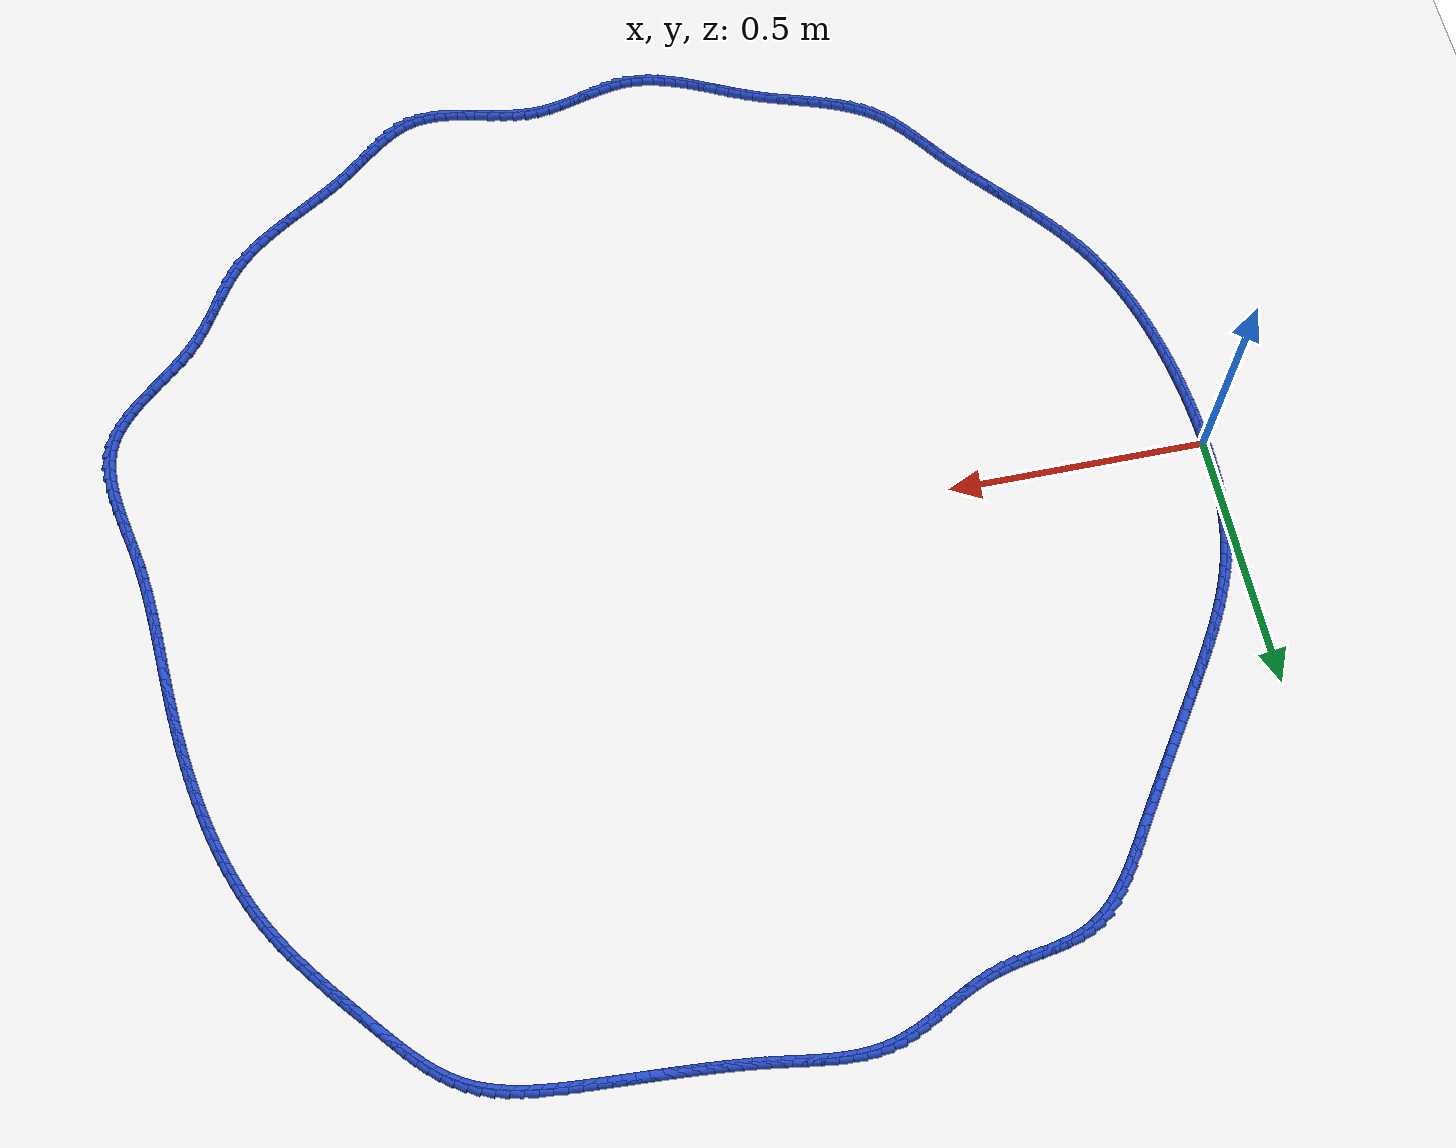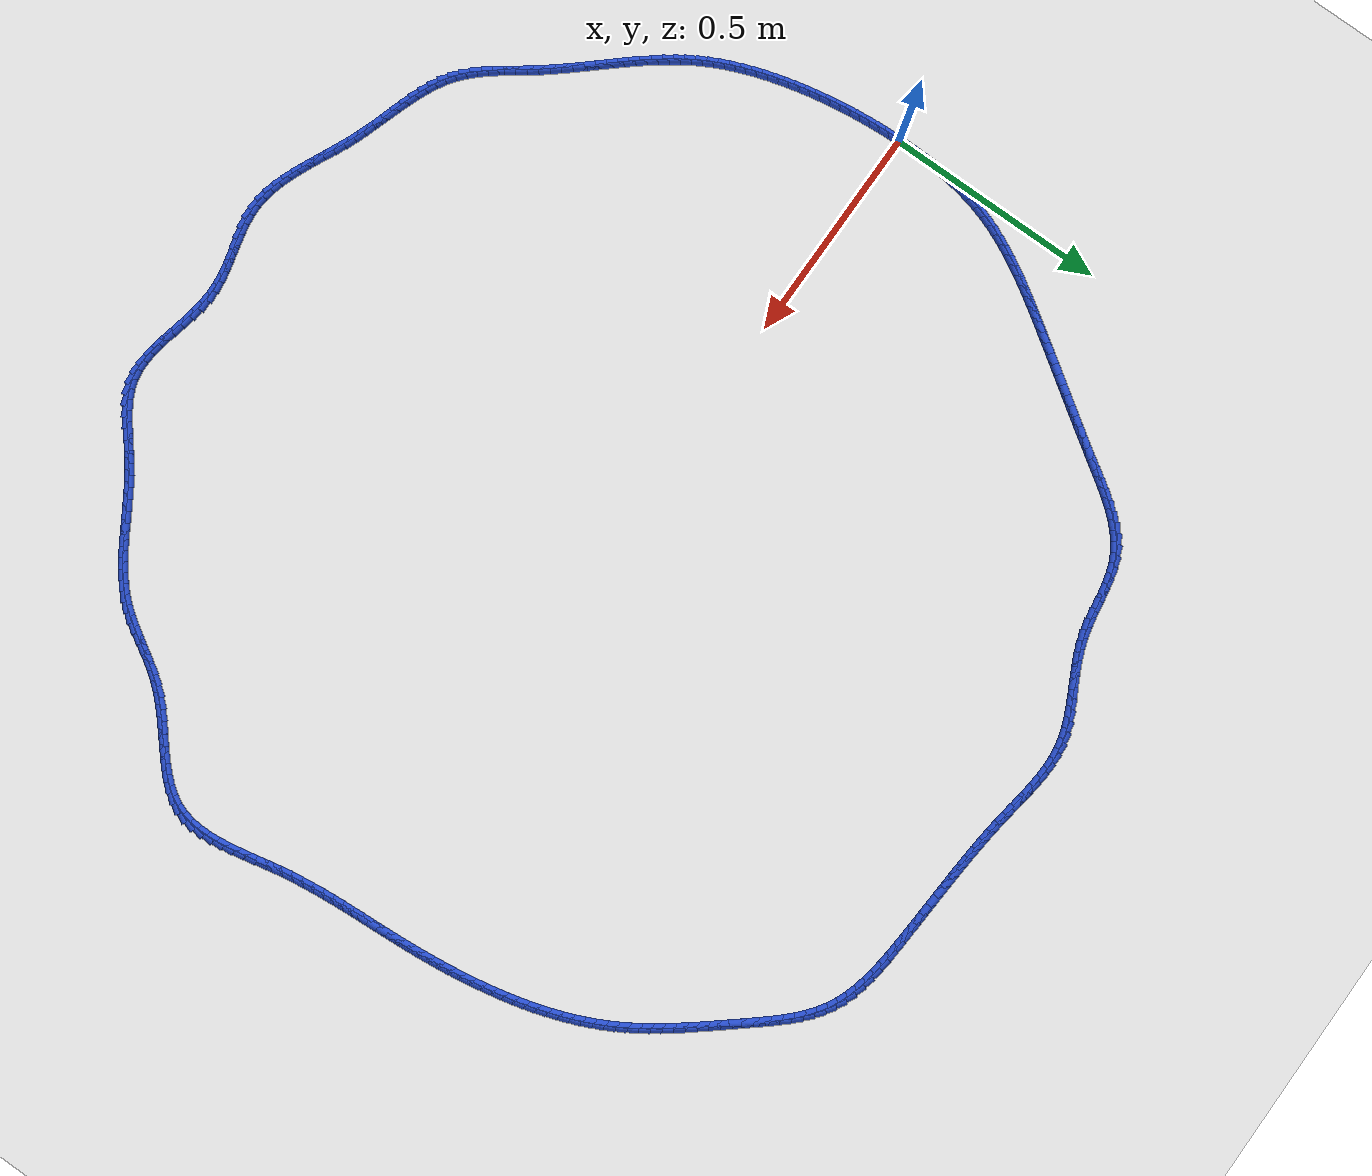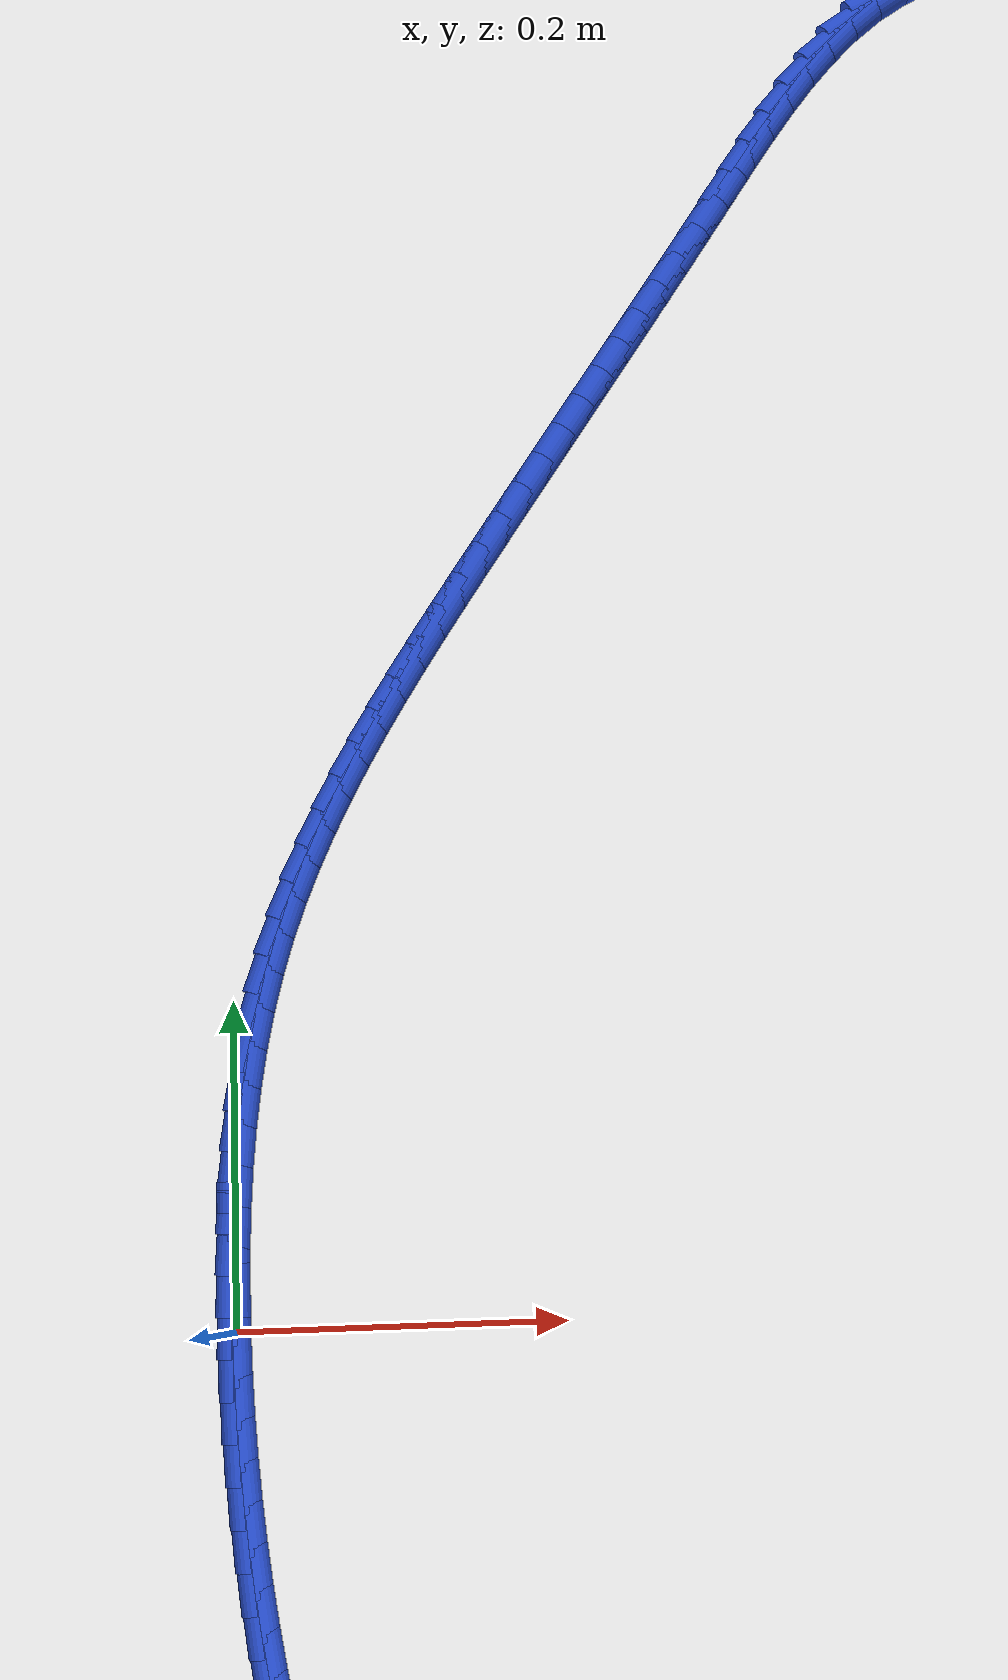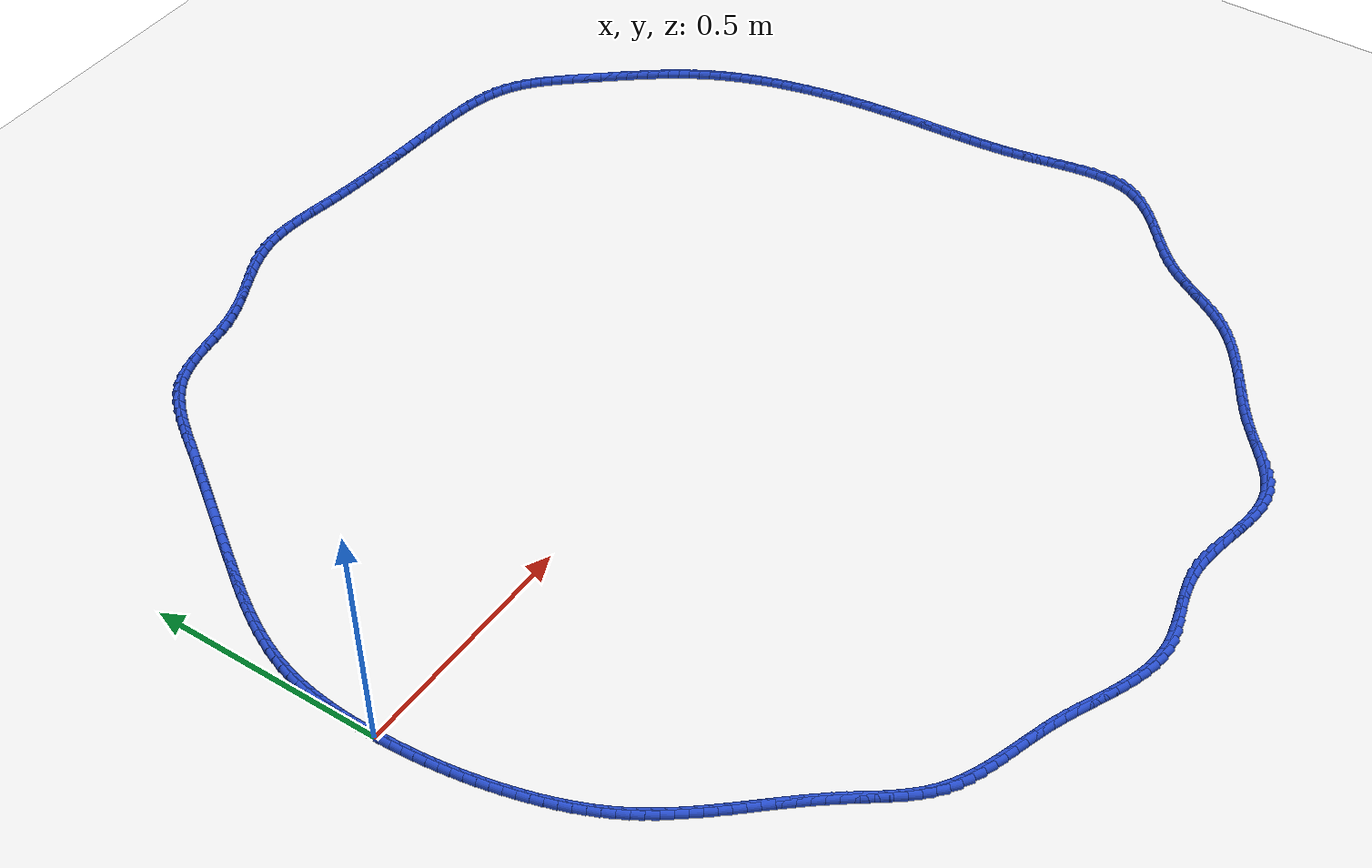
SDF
<sdf version="1.6">
 <world name="default">
  <light name="sun" type="directional">
   <pose>0 0 10 0 -0 0</pose>
   <diffuse>0.8 0.8 0.8 1</diffuse>
   <specular>0.2 0.2 0.2 1</specular>
   <attenuation>
    <range>1000</range>
    <constant>0.9</constant>
    <linear>0.01</linear>
    <quadratic>0.001</quadratic>
   </attenuation>
   <direction>-0.5 0.1 -0.9</direction>
  </light>
  <model name="ground_plane">
   <static>1</static>
   <link name="link">
    <collision name="collision">
     <geometry><plane><normal>0 0 1</normal><size>100 100</size></plane></geometry>
     <surface><friction><ode><mu>100</mu><mu2>50</mu2></ode></friction></surface>
    </collision>
    <visual name="visual">
     <cast_shadows>0</cast_shadows>
     <geometry><plane><normal>0 0 1</normal><size>100 100</size></plane></geometry>
     <material>
      <script><uri>file://media/materials/scripts/gazebo.material</uri><name>Gazebo/WhiteGlow</name></script>
     </material>
    </visual>
   </link>
  </model>
  <gravity>0 0 -9.8</gravity>
  <magnetic_field>6e-06 2.3e-05 -4.2e-05</magnetic_field>
  <atmosphere type="adiabatic"/>
  <physics name="default_physics" default="0" type="ode">
   <max_step_size>0.001</max_step_size>
   <real_time_factor>1</real_time_factor>
   <real_time_update_rate>1000</real_time_update_rate>
  </physics>
  <scene><ambient>0.4 0.4 0.4 1</ambient><background>0.7 0.7 0.7 1</background><shadows>1</shadows></scene>
  <spherical_coordinates>
   <surface_model>EARTH_WGS84</surface_model>
   <latitude_deg>0</latitude_deg>
   <longitude_deg>0</longitude_deg>
   <elevation>0</elevation>
   <heading_deg>0</heading_deg>
  </spherical_coordinates>
  <model name="line">
   <link name="link_0">
    <pose>8.239936510889834e-18 4.163336342344337e-17 0.01 0 1.57 -1.5604847739984256</pose>
    <collision name="collision">
     <geometry><cylinder><radius>0.01</radius><length>0.08</length></cylinder></geometry>
    </collision>
    <visual name="visual">
     <material>
      <script><name>Gazebo/Blue</name><uri>file://media/materials/scripts/gazebo.material</uri></script>
     </material>
     <geometry><cylinder><radius>0.01</radius><length>0.08</length></cylinder></geometry>
    </visual>
   </link>
   <link name="link_1">
    <pose>-0.00025069984554152266 0.02431165945086034 0.01 0 1.57 1.5592620202173926</pose>
    <collision name="collision">
     <geometry><cylinder><radius>0.01</radius><length>0.08</length></cylinder></geometry>
    </collision>
    <visual name="visual">
     <material>
      <script><name>Gazebo/Blue</name><uri>file://media/materials/scripts/gazebo.material</uri></script>
     </material>
     <geometry><cylinder><radius>0.01</radius><length>0.08</length></cylinder></geometry>
    </visual>
   </link>
   <link name="link_2">
    <pose>3.0164865778178077e-05 0.04866095638405373 0.01 0 1.57 1.5345862038355789</pose>
    <collision name="collision">
     <geometry><cylinder><radius>0.01</radius><length>0.08</length></cylinder></geometry>
    </collision>
    <visual name="visual">
     <material>
      <script><name>Gazebo/Blue</name><uri>file://media/materials/scripts/gazebo.material</uri></script>
     </material>
     <geometry><cylinder><radius>0.01</radius><length>0.08</length></cylinder></geometry>
    </visual>
   </link>
   <link name="link_3">
    <pose>0.0009119169149197662 0.0730012945802726 0.01 0 1.57 1.5069763396968603</pose>
    <collision name="collision">
     <geometry><cylinder><radius>0.01</radius><length>0.08</length></cylinder></geometry>
    </collision>
    <visual name="visual">
     <material>
      <script><name>Gazebo/Blue</name><uri>file://media/materials/scripts/gazebo.material</uri></script>
     </material>
     <geometry><cylinder><radius>0.01</radius><length>0.08</length></cylinder></geometry>
    </visual>
   </link>
   <link name="link_4">
    <pose>0.0024638790828438928 0.09728607782020932 0.01 0 1.57 1.4763205357476048</pose>
    <collision name="collision">
     <geometry><cylinder><radius>0.01</radius><length>0.08</length></cylinder></geometry>
    </collision>
    <visual name="visual">
     <material>
      <script><name>Gazebo/Blue</name><uri>file://media/materials/scripts/gazebo.material</uri></script>
     </material>
     <geometry><cylinder><radius>0.01</radius><length>0.08</length></cylinder></geometry>
    </visual>
   </link>
   <link name="link_5">
    <pose>0.004755374150511214 0.12146870988455631 0.01 0 1.57 1.442505662867456</pose>
    <collision name="collision">
     <geometry><cylinder><radius>0.01</radius><length>0.08</length></cylinder></geometry>
    </collision>
    <visual name="visual">
     <material>
      <script><name>Gazebo/Blue</name><uri>file://media/materials/scripts/gazebo.material</uri></script>
     </material>
     <geometry><cylinder><radius>0.01</radius><length>0.08</length></cylinder></geometry>
    </visual>
   </link>
   <link name="link_6">
    <pose>0.007855724898882385 0.14550259455400597 0.01 0 1.57 1.4054256627517405</pose>
    <collision name="collision">
     <geometry><cylinder><radius>0.01</radius><length>0.08</length></cylinder></geometry>
    </collision>
    <visual name="visual">
     <material>
      <script><name>Gazebo/Blue</name><uri>file://media/materials/scripts/gazebo.material</uri></script>
     </material>
     <geometry><cylinder><radius>0.01</radius><length>0.08</length></cylinder></geometry>
    </visual>
   </link>
   <link name="link_7">
    <pose>0.011834254108918058 0.16934113560925065 0.01 0 1.57 1.3649918923019504</pose>
    <collision name="collision">
     <geometry><cylinder><radius>0.01</radius><length>0.08</length></cylinder></geometry>
    </collision>
    <visual name="visual">
     <material>
      <script><name>Gazebo/Blue</name><uri>file://media/materials/scripts/gazebo.material</uri></script>
     </material>
     <geometry><cylinder><radius>0.01</radius><length>0.08</length></cylinder></geometry>
    </visual>
   </link>
   <link name="link_8">
    <pose>0.016760284561578877 0.19293773683098275 0.01 0 1.57 1.3211456311322216</pose>
    <collision name="collision">
     <geometry><cylinder><radius>0.01</radius><length>0.08</length></cylinder></geometry>
    </collision>
    <visual name="visual">
     <material>
      <script><name>Gazebo/Blue</name><uri>file://media/materials/scripts/gazebo.material</uri></script>
     </material>
     <geometry><cylinder><radius>0.01</radius><length>0.08</length></cylinder></geometry>
    </visual>
   </link>
   <link name="link_9">
    <pose>0.02270313903782551 0.21624580199989474 0.01 0 1.57 1.273939900634041</pose>
    <collision name="collision">
     <geometry><cylinder><radius>0.01</radius><length>0.08</length></cylinder></geometry>
    </collision>
    <visual name="visual">
     <material>
      <script><name>Gazebo/Blue</name><uri>file://media/materials/scripts/gazebo.material</uri></script>
     </material>
     <geometry><cylinder><radius>0.01</radius><length>0.08</length></cylinder></geometry>
    </visual>
   </link>
   <link name="link_10">
    <pose>0.02973062624675743 0.23921931411991565 0.01 0 1.57 1.2264510314620878</pose>
    <collision name="collision">
     <geometry><cylinder><radius>0.01</radius><length>0.08</length></cylinder></geometry>
    </collision>
    <visual name="visual">
     <material>
      <script><name>Gazebo/Blue</name><uri>file://media/materials/scripts/gazebo.material</uri></script>
     </material>
     <geometry><cylinder><radius>0.01</radius><length>0.08</length></cylinder></geometry>
    </visual>
   </link>
   <link name="link_11">
    <pose>0.0378425423900538 0.261838275055571 0.01 0 1.57 1.1829624203381641</pose>
    <collision name="collision">
     <geometry><cylinder><radius>0.01</radius><length>0.08</length></cylinder></geometry>
    </collision>
    <visual name="visual">
     <material>
      <script><name>Gazebo/Blue</name><uri>file://media/materials/scripts/gazebo.material</uri></script>
     </material>
     <geometry><cylinder><radius>0.01</radius><length>0.08</length></cylinder></geometry>
    </visual>
   </link>
   <link name="link_12">
    <pose>0.04694463993999588 0.2841186640346382 0.01 0 1.57 1.1438245514091114</pose>
    <collision name="collision">
     <geometry><cylinder><radius>0.01</radius><length>0.08</length></cylinder></geometry>
    </collision>
    <visual name="visual">
     <material>
      <script><name>Gazebo/Blue</name><uri>file://media/materials/scripts/gazebo.material</uri></script>
     </material>
     <geometry><cylinder><radius>0.01</radius><length>0.08</length></cylinder></geometry>
    </visual>
   </link>
   <link name="link_13">
    <pose>0.05693577904941704 0.3060790970101928 0.01 0 1.57 1.1090159330003566</pose>
    <collision name="collision">
     <geometry><cylinder><radius>0.01</radius><length>0.08</length></cylinder></geometry>
    </collision>
    <visual name="visual">
     <material>
      <script><name>Gazebo/Blue</name><uri>file://media/materials/scripts/gazebo.material</uri></script>
     </material>
     <geometry><cylinder><radius>0.01</radius><length>0.08</length></cylinder></geometry>
    </visual>
   </link>
   <link name="link_14">
    <pose>0.06771481987115063 0.32773818993531045 0.01 0 1.57 1.0784719921911587</pose>
    <collision name="collision">
     <geometry><cylinder><radius>0.01</radius><length>0.08</length></cylinder></geometry>
    </collision>
    <visual name="visual">
     <material>
      <script><name>Gazebo/Blue</name><uri>file://media/materials/scripts/gazebo.material</uri></script>
     </material>
     <geometry><cylinder><radius>0.01</radius><length>0.08</length></cylinder></geometry>
    </visual>
   </link>
   <link name="link_15">
    <pose>0.07918062255802999 0.3491145587630667 0.01 0 1.57 1.0521046699254197</pose>
    <collision name="collision">
     <geometry><cylinder><radius>0.01</radius><length>0.08</length></cylinder></geometry>
    </collision>
    <visual name="visual">
     <material>
      <script><name>Gazebo/Blue</name><uri>file://media/materials/scripts/gazebo.material</uri></script>
     </material>
     <geometry><cylinder><radius>0.01</radius><length>0.08</length></cylinder></geometry>
    </visual>
   </link>
   <link name="link_16">
    <pose>0.09123204726288842 0.37022681944653696 0.01 0 1.57 1.0298186468648656</pose>
    <collision name="collision">
     <geometry><cylinder><radius>0.01</radius><length>0.08</length></cylinder></geometry>
    </collision>
    <visual name="visual">
     <material>
      <script><name>Gazebo/Blue</name><uri>file://media/materials/scripts/gazebo.material</uri></script>
     </material>
     <geometry><cylinder><radius>0.01</radius><length>0.08</length></cylinder></geometry>
    </visual>
   </link>
   <link name="link_17">
    <pose>0.10376795413855934 0.39109358793879706 0.01 0 1.57 1.011524299428808</pose>
    <collision name="collision">
     <geometry><cylinder><radius>0.01</radius><length>0.08</length></cylinder></geometry>
    </collision>
    <visual name="visual">
     <material>
      <script><name>Gazebo/Blue</name><uri>file://media/materials/scripts/gazebo.material</uri></script>
     </material>
     <geometry><cylinder><radius>0.01</radius><length>0.08</length></cylinder></geometry>
    </visual>
   </link>
   <link name="link_18">
    <pose>0.11668720333787597 0.41173348019292233 0.01 0 1.57 0.9971478171736029</pose>
    <collision name="collision">
     <geometry><cylinder><radius>0.01</radius><length>0.08</length></cylinder></geometry>
    </collision>
    <visual name="visual">
     <material>
      <script><name>Gazebo/Blue</name><uri>file://media/materials/scripts/gazebo.material</uri></script>
     </material>
     <geometry><cylinder><radius>0.01</radius><length>0.08</length></cylinder></geometry>
    </visual>
   </link>
   <link name="link_19">
    <pose>0.12988865501367183 0.43216511216198866 0.01 0 1.57 0.9866390414312071</pose>
    <collision name="collision">
     <geometry><cylinder><radius>0.01</radius><length>0.08</length></cylinder></geometry>
    </collision>
    <visual name="visual">
     <material>
      <script><name>Gazebo/Blue</name><uri>file://media/materials/scripts/gazebo.material</uri></script>
     </material>
     <geometry><cylinder><radius>0.01</radius><length>0.08</length></cylinder></geometry>
    </visual>
   </link>
   <link name="link_20">
    <pose>0.14327116931878012 0.45240709979907134 0.01 0 1.57 0.9799775833858296</pose>
    <collision name="collision">
     <geometry><cylinder><radius>0.01</radius><length>0.08</length></cylinder></geometry>
    </collision>
    <visual name="visual">
     <material>
      <script><name>Gazebo/Blue</name><uri>file://media/materials/scripts/gazebo.material</uri></script>
     </material>
     <geometry><cylinder><radius>0.01</radius><length>0.08</length></cylinder></geometry>
    </visual>
   </link>
   <link name="link_21">
    <pose>0.15673360640603423 0.47247805905724605 0.01 0 1.57 0.9767106705080332</pose>
    <collision name="collision">
     <geometry><cylinder><radius>0.01</radius><length>0.08</length></cylinder></geometry>
    </collision>
    <visual name="visual">
     <material>
      <script><name>Gazebo/Blue</name><uri>file://media/materials/scripts/gazebo.material</uri></script>
     </material>
     <geometry><cylinder><radius>0.01</radius><length>0.08</length></cylinder></geometry>
    </visual>
   </link>
   <link name="link_22">
    <pose>0.17018978497747667 0.49239870154055243 0.01 0 1.57 0.9745750853264366</pose>
    <collision name="collision">
     <geometry><cylinder><radius>0.01</radius><length>0.08</length></cylinder></geometry>
    </collision>
    <visual name="visual">
     <material>
      <script><name>Gazebo/Blue</name><uri>file://media/materials/scripts/gazebo.material</uri></script>
     </material>
     <geometry><cylinder><radius>0.01</radius><length>0.08</length></cylinder></geometry>
    </visual>
   </link>
   <link name="link_23">
    <pose>0.18362704603289876 0.5122000391215921 0.01 0 1.57 0.9728841787584968</pose>
    <collision name="collision">
     <geometry><cylinder><radius>0.01</radius><length>0.08</length></cylinder></geometry>
    </collision>
    <visual name="visual">
     <material>
      <script><name>Gazebo/Blue</name><uri>file://media/materials/scripts/gazebo.material</uri></script>
     </material>
     <geometry><cylinder><radius>0.01</radius><length>0.08</length></cylinder></geometry>
    </visual>
   </link>
   <link name="link_24">
    <pose>0.19705528166166544 0.5319162430176296 0.01 0 1.57 0.9716492080914787</pose>
    <collision name="collision">
     <geometry><cylinder><radius>0.01</radius><length>0.08</length></cylinder></geometry>
    </collision>
    <visual name="visual">
     <material>
      <script><name>Gazebo/Blue</name><uri>file://media/materials/scripts/gazebo.material</uri></script>
     </material>
     <geometry><cylinder><radius>0.01</radius><length>0.08</length></cylinder></geometry>
    </visual>
   </link>
   <link name="link_25">
    <pose>0.2104843898975176 0.55158148527872 0.01 0 1.57 0.9708778305333526</pose>
    <collision name="collision">
     <geometry><cylinder><radius>0.01</radius><length>0.08</length></cylinder></geometry>
    </collision>
    <visual name="visual">
     <material>
      <script><name>Gazebo/Blue</name><uri>file://media/materials/scripts/gazebo.material</uri></script>
     </material>
     <geometry><cylinder><radius>0.01</radius><length>0.08</length></cylinder></geometry>
    </visual>
   </link>
   <link name="link_26">
    <pose>0.22392426877419597 0.5712299379549174 0.01 0 1.57 0.970573783664825</pose>
    <collision name="collision">
     <geometry><cylinder><radius>0.01</radius><length>0.08</length></cylinder></geometry>
    </collision>
    <visual name="visual">
     <material>
      <script><name>Gazebo/Blue</name><uri>file://media/materials/scripts/gazebo.material</uri></script>
     </material>
     <geometry><cylinder><radius>0.01</radius><length>0.08</length></cylinder></geometry>
    </visual>
   </link>
   <link name="link_27">
    <pose>0.23738481632544145 0.5908957730962775 0.01 0 1.57 0.9707368311062204</pose>
    <collision name="collision">
     <geometry><cylinder><radius>0.01</radius><length>0.08</length></cylinder></geometry>
    </collision>
    <visual name="visual">
     <material>
      <script><name>Gazebo/Blue</name><uri>file://media/materials/scripts/gazebo.material</uri></script>
     </material>
     <geometry><cylinder><radius>0.01</radius><length>0.08</length></cylinder></geometry>
    </visual>
   </link>
   <link name="link_28">
    <pose>0.25087593058499497 0.6106131627528549 0.01 0 1.57 0.9713627893692124</pose>
    <collision name="collision">
     <geometry><cylinder><radius>0.01</radius><length>0.08</length></cylinder></geometry>
    </collision>
    <visual name="visual">
     <material>
      <script><name>Gazebo/Blue</name><uri>file://media/materials/scripts/gazebo.material</uri></script>
     </material>
     <geometry><cylinder><radius>0.01</radius><length>0.08</length></cylinder></geometry>
    </visual>
   </link>
   <link name="link_29">
    <pose>0.2644075095865972 0.6304162789747041 0.01 0 1.57 0.9724436344190517</pose>
    <collision name="collision">
     <geometry><cylinder><radius>0.01</radius><length>0.08</length></cylinder></geometry>
    </collision>
    <visual name="visual">
     <material>
      <script><name>Gazebo/Blue</name><uri>file://media/materials/scripts/gazebo.material</uri></script>
     </material>
     <geometry><cylinder><radius>0.01</radius><length>0.08</length></cylinder></geometry>
    </visual>
   </link>
   <link name="link_30">
    <pose>0.27798945136398906 0.6503392938118804 0.01 0 1.57 0.9739676836178367</pose>
    <collision name="collision">
     <geometry><cylinder><radius>0.01</radius><length>0.08</length></cylinder></geometry>
    </collision>
    <visual name="visual">
     <material>
      <script><name>Gazebo/Blue</name><uri>file://media/materials/scripts/gazebo.material</uri></script>
     </material>
     <geometry><cylinder><radius>0.01</radius><length>0.08</length></cylinder></geometry>
    </visual>
   </link>
   <link name="link_31">
    <pose>0.2916316539509114 0.6704163793144386 0.01 0 1.57 0.9759198461228842</pose>
    <collision name="collision">
     <geometry><cylinder><radius>0.01</radius><length>0.08</length></cylinder></geometry>
    </collision>
    <visual name="visual">
     <material>
      <script><name>Gazebo/Blue</name><uri>file://media/materials/scripts/gazebo.material</uri></script>
     </material>
     <geometry><cylinder><radius>0.01</radius><length>0.08</length></cylinder></geometry>
    </visual>
   </link>
   <link name="link_32">
    <pose>0.30534401538110506 0.6906817075324332 0.01 0 1.57 0.9782819326101947</pose>
    <collision name="collision">
     <geometry><cylinder><radius>0.01</radius><length>0.08</length></cylinder></geometry>
    </collision>
    <visual name="visual">
     <material>
      <script><name>Gazebo/Blue</name><uri>file://media/materials/scripts/gazebo.material</uri></script>
     </material>
     <geometry><cylinder><radius>0.01</radius><length>0.08</length></cylinder></geometry>
    </visual>
   </link>
   <link name="link_33">
    <pose>0.31913643368831096 0.7111694505159197 0.01 0 1.57 0.9810329977839432</pose>
    <collision name="collision">
     <geometry><cylinder><radius>0.01</radius><length>0.08</length></cylinder></geometry>
    </collision>
    <visual name="visual">
     <material>
      <script><name>Gazebo/Blue</name><uri>file://media/materials/scripts/gazebo.material</uri></script>
     </material>
     <geometry><cylinder><radius>0.01</radius><length>0.08</length></cylinder></geometry>
    </visual>
   </link>
   <link name="link_34">
    <pose>0.33301880707826526 0.7319137798672907 0.01 0 1.57 0.9817148681055523</pose>
    <collision name="collision">
     <geometry><cylinder><radius>0.01</radius><length>0.08</length></cylinder></geometry>
    </collision>
    <visual name="visual">
     <material>
      <script><name>Gazebo/Blue</name><uri>file://media/materials/scripts/gazebo.material</uri></script>
     </material>
     <geometry><cylinder><radius>0.01</radius><length>0.08</length></cylinder></geometry>
    </visual>
   </link>
   <link name="link_35">
    <pose>0.347028037138563 0.7528785840286789 0.01 0 1.57 0.971191980364358</pose>
    <collision name="collision">
     <geometry><cylinder><radius>0.01</radius><length>0.08</length></cylinder></geometry>
    </collision>
    <visual name="visual">
     <material>
      <script><name>Gazebo/Blue</name><uri>file://media/materials/scripts/gazebo.material</uri></script>
     </material>
     <geometry><cylinder><radius>0.01</radius><length>0.08</length></cylinder></geometry>
    </visual>
   </link>
   <link name="link_36">
    <pose>0.3613030915162859 0.7737620985971946 0.01 0 1.57 0.9471340086800905</pose>
    <collision name="collision">
     <geometry><cylinder><radius>0.01</radius><length>0.08</length></cylinder></geometry>
    </collision>
    <visual name="visual">
     <material>
      <script><name>Gazebo/Blue</name><uri>file://media/materials/scripts/gazebo.material</uri></script>
     </material>
     <geometry><cylinder><radius>0.01</radius><length>0.08</length></cylinder></geometry>
    </visual>
   </link>
   <link name="link_37">
    <pose>0.37600704852087685 0.7941998050469435 0.01 0 1.57 0.9087952251910757</pose>
    <collision name="collision">
     <geometry><cylinder><radius>0.01</radius><length>0.08</length></cylinder></geometry>
    </collision>
    <visual name="visual">
     <material>
      <script><name>Gazebo/Blue</name><uri>file://media/materials/scripts/gazebo.material</uri></script>
     </material>
     <geometry><cylinder><radius>0.01</radius><length>0.08</length></cylinder></geometry>
    </visual>
   </link>
   <link name="link_38">
    <pose>0.3913029864617782 0.8138271848520312 0.01 0 1.57 0.8548887473618845</pose>
    <collision name="collision">
     <geometry><cylinder><radius>0.01</radius><length>0.08</length></cylinder></geometry>
    </collision>
    <visual name="visual">
     <material>
      <script><name>Gazebo/Blue</name><uri>file://media/materials/scripts/gazebo.material</uri></script>
     </material>
     <geometry><cylinder><radius>0.01</radius><length>0.08</length></cylinder></geometry>
    </visual>
   </link>
   <link name="link_39">
    <pose>0.4073539836484328 0.8322797194865638 0.01 0 1.57 0.7837464531093727</pose>
    <collision name="collision">
     <geometry><cylinder><radius>0.01</radius><length>0.08</length></cylinder></geometry>
    </collision>
    <visual name="visual">
     <material>
      <script><name>Gazebo/Blue</name><uri>file://media/materials/scripts/gazebo.material</uri></script>
     </material>
     <geometry><cylinder><radius>0.01</radius><length>0.08</length></cylinder></geometry>
    </visual>
   </link>
   <link name="link_40">
    <pose>0.4243231183902832 0.8491928904246464 0.01 0 1.57 0.693669161298863</pose>
    <collision name="collision">
     <geometry><cylinder><radius>0.01</radius><length>0.08</length></cylinder></geometry>
    </collision>
    <visual name="visual">
     <material>
      <script><name>Gazebo/Blue</name><uri>file://media/materials/scripts/gazebo.material</uri></script>
     </material>
     <geometry><cylinder><radius>0.01</radius><length>0.08</length></cylinder></geometry>
    </visual>
   </link>
   <link name="link_41">
    <pose>0.44237346899677205 0.8642021791403851 0.01 0 1.57 0.5836048326432384</pose>
    <collision name="collision">
     <geometry><cylinder><radius>0.01</radius><length>0.08</length></cylinder></geometry>
    </collision>
    <visual name="visual">
     <material>
      <script><name>Gazebo/Blue</name><uri>file://media/materials/scripts/gazebo.material</uri></script>
     </material>
     <geometry><cylinder><radius>0.01</radius><length>0.08</length></cylinder></geometry>
    </visual>
   </link>
   <link name="link_42">
    <pose>0.4616681137773423 0.876943067107886 0.01 0 1.57 0.4562226401614573</pose>
    <collision name="collision">
     <geometry><cylinder><radius>0.01</radius><length>0.08</length></cylinder></geometry>
    </collision>
    <visual name="visual">
     <material>
      <script><name>Gazebo/Blue</name><uri>file://media/materials/scripts/gazebo.material</uri></script>
     </material>
     <geometry><cylinder><radius>0.01</radius><length>0.08</length></cylinder></geometry>
    </visual>
   </link>
   <link name="link_43">
    <pose>0.48235092485361825 0.8870932176279565 0.01 0 1.57 0.3401770621577796</pose>
    <collision name="collision">
     <geometry><cylinder><radius>0.01</radius><length>0.08</length></cylinder></geometry>
    </collision>
    <visual name="visual">
     <material>
      <script><name>Gazebo/Blue</name><uri>file://media/materials/scripts/gazebo.material</uri></script>
     </material>
     <geometry><cylinder><radius>0.01</radius><length>0.08</length></cylinder></geometry>
    </visual>
   </link>
   <link name="link_44">
    <pose>0.5043204753942071 0.8948690348501633 0.01 0 1.57 0.2549254770216151</pose>
    <collision name="collision">
     <geometry><cylinder><radius>0.01</radius><length>0.08</length></cylinder></geometry>
    </collision>
    <visual name="visual">
     <material>
      <script><name>Gazebo/Blue</name><uri>file://media/materials/scripts/gazebo.material</uri></script>
     </material>
     <geometry><cylinder><radius>0.01</radius><length>0.08</length></cylinder></geometry>
    </visual>
   </link>
   <link name="link_45">
    <pose>0.5273059523472255 0.9008589394984259 0.01 0 1.57 0.1995977254259138</pose>
    <collision name="collision">
     <geometry><cylinder><radius>0.01</radius><length>0.08</length></cylinder></geometry>
    </collision>
    <visual name="visual">
     <material>
      <script><name>Gazebo/Blue</name><uri>file://media/materials/scripts/gazebo.material</uri></script>
     </material>
     <geometry><cylinder><radius>0.01</radius><length>0.08</length></cylinder></geometry>
    </visual>
   </link>
   <link name="link_46">
    <pose>0.5510331746573587 0.9056587493157112 0.01 0 1.57 0.1721002973887404</pose>
    <collision name="collision">
     <geometry><cylinder><radius>0.01</radius><length>0.08</length></cylinder></geometry>
    </collision>
    <visual name="visual">
     <material>
      <script><name>Gazebo/Blue</name><uri>file://media/materials/scripts/gazebo.material</uri></script>
     </material>
     <geometry><cylinder><radius>0.01</radius><length>0.08</length></cylinder></geometry>
    </visual>
   </link>
   <link name="link_47">
    <pose>0.5752279612692919 0.9098642820449867 0.01 0 1.57 0.17082347116319607</pose>
    <collision name="collision">
     <geometry><cylinder><radius>0.01</radius><length>0.08</length></cylinder></geometry>
    </collision>
    <visual name="visual">
     <material>
      <script><name>Gazebo/Blue</name><uri>file://media/materials/scripts/gazebo.material</uri></script>
     </material>
     <geometry><cylinder><radius>0.01</radius><length>0.08</length></cylinder></geometry>
    </visual>
   </link>
   <link name="link_48">
    <pose>0.59961613112771 0.9140713554292188 0.01 0 1.57 0.19513808211061756</pose>
    <collision name="collision">
     <geometry><cylinder><radius>0.01</radius><length>0.08</length></cylinder></geometry>
    </collision>
    <visual name="visual">
     <material>
      <script><name>Gazebo/Blue</name><uri>file://media/materials/scripts/gazebo.material</uri></script>
     </material>
     <geometry><cylinder><radius>0.01</radius><length>0.08</length></cylinder></geometry>
    </visual>
   </link>
   <link name="link_49">
    <pose>0.6239235031772981 0.9188757872113745 0.01 0 1.57 0.24535229595635472</pose>
    <collision name="collision">
     <geometry><cylinder><radius>0.01</radius><length>0.08</length></cylinder></geometry>
    </collision>
    <visual name="visual">
     <material>
      <script><name>Gazebo/Blue</name><uri>file://media/materials/scripts/gazebo.material</uri></script>
     </material>
     <geometry><cylinder><radius>0.01</radius><length>0.08</length></cylinder></geometry>
    </visual>
   </link>
   <link name="link_50">
    <pose>0.647875896362741 0.9248733951344213 0.01 0 1.57 0.31780580590979524</pose>
    <collision name="collision">
     <geometry><cylinder><radius>0.01</radius><length>0.08</length></cylinder></geometry>
    </collision>
    <visual name="visual">
     <material>
      <script><name>Gazebo/Blue</name><uri>file://media/materials/scripts/gazebo.material</uri></script>
     </material>
     <geometry><cylinder><radius>0.01</radius><length>0.08</length></cylinder></geometry>
    </visual>
   </link>
   <link name="link_51">
    <pose>0.6712379273793113 0.9325584757030204 0.01 0 1.57 0.3833589825987224</pose>
    <collision name="collision">
     <geometry><cylinder><radius>0.01</radius><length>0.08</length></cylinder></geometry>
    </collision>
    <visual name="visual">
     <material>
      <script><name>Gazebo/Blue</name><uri>file://media/materials/scripts/gazebo.material</uri></script>
     </material>
     <geometry><cylinder><radius>0.01</radius><length>0.08</length></cylinder></geometry>
    </visual>
   </link>
   <link name="link_52">
    <pose>0.6940317226193609 0.9417515053439345 0.01 0 1.57 0.4298378916335147</pose>
    <collision name="collision">
     <geometry><cylinder><radius>0.01</radius><length>0.08</length></cylinder></geometry>
    </collision>
    <visual name="visual">
     <material>
      <script><name>Gazebo/Blue</name><uri>file://media/materials/scripts/gazebo.material</uri></script>
     </material>
     <geometry><cylinder><radius>0.01</radius><length>0.08</length></cylinder></geometry>
    </visual>
   </link>
   <link name="link_53">
    <pose>0.7163843036406028 0.9519984835640382 0.01 0 1.57 0.45733984747566964</pose>
    <collision name="collision">
     <geometry><cylinder><radius>0.01</radius><length>0.08</length></cylinder></geometry>
    </collision>
    <visual name="visual">
     <material>
      <script><name>Gazebo/Blue</name><uri>file://media/materials/scripts/gazebo.material</uri></script>
     </material>
     <geometry><cylinder><radius>0.01</radius><length>0.08</length></cylinder></geometry>
    </visual>
   </link>
   <link name="link_54">
    <pose>0.7384229989419155 0.9628446067038728 0.01 0 1.57 0.4660023231944812</pose>
    <collision name="collision">
     <geometry><cylinder><radius>0.01</radius><length>0.08</length></cylinder></geometry>
    </collision>
    <visual name="visual">
     <material>
      <script><name>Gazebo/Blue</name><uri>file://media/materials/scripts/gazebo.material</uri></script>
     </material>
     <geometry><cylinder><radius>0.01</radius><length>0.08</length></cylinder></geometry>
    </visual>
   </link>
   <link name="link_55">
    <pose>0.7602751370221769 0.9738350711039795 0.01 0 1.57 0.4556702824359259</pose>
    <collision name="collision">
     <geometry><cylinder><radius>0.01</radius><length>0.08</length></cylinder></geometry>
    </collision>
    <visual name="visual">
     <material>
      <script><name>Gazebo/Blue</name><uri>file://media/materials/scripts/gazebo.material</uri></script>
     </material>
     <geometry><cylinder><radius>0.01</radius><length>0.08</length></cylinder></geometry>
    </visual>
   </link>
   <link name="link_56">
    <pose>0.782068046380265 0.9845150731048986 0.01 0 1.57 0.4257898629789418</pose>
    <collision name="collision">
     <geometry><cylinder><radius>0.01</radius><length>0.08</length></cylinder></geometry>
    </collision>
    <visual name="visual">
     <material>
      <script><name>Gazebo/Blue</name><uri>file://media/materials/scripts/gazebo.material</uri></script>
     </material>
     <geometry><cylinder><radius>0.01</radius><length>0.08</length></cylinder></geometry>
    </visual>
   </link>
   <link name="link_57">
    <pose>0.8039290555150573 0.9944298090471714 0.01 0 1.57 0.37549712874481705</pose>
    <collision name="collision">
     <geometry><cylinder><radius>0.01</radius><length>0.08</length></cylinder></geometry>
    </collision>
    <visual name="visual">
     <material>
      <script><name>Gazebo/Blue</name><uri>file://media/materials/scripts/gazebo.material</uri></script>
     </material>
     <geometry><cylinder><radius>0.01</radius><length>0.08</length></cylinder></geometry>
    </visual>
   </link>
   <link name="link_58">
    <pose>0.8259854929254329 1.003124475271339 0.01 0 1.57 0.3039549364498188</pose>
    <collision name="collision">
     <geometry><cylinder><radius>0.01</radius><length>0.08</length></cylinder></geometry>
    </collision>
    <visual name="visual">
     <material>
      <script><name>Gazebo/Blue</name><uri>file://media/materials/scripts/gazebo.material</uri></script>
     </material>
     <geometry><cylinder><radius>0.01</radius><length>0.08</length></cylinder></geometry>
    </visual>
   </link>
   <link name="link_59">
    <pose>0.848364687110269 1.0101442681179424 0.01 0 1.57 0.21136150523633418</pose>
    <collision name="collision">
     <geometry><cylinder><radius>0.01</radius><length>0.08</length></cylinder></geometry>
    </collision>
    <visual name="visual">
     <material>
      <script><name>Gazebo/Blue</name><uri>file://media/materials/scripts/gazebo.material</uri></script>
     </material>
     <geometry><cylinder><radius>0.01</radius><length>0.08</length></cylinder></geometry>
    </visual>
   </link>
   <link name="link_60">
    <pose>0.8711918874987525 1.0150422141373594 0.01 0 1.57 0.11340508237841727</pose>
    <collision name="collision">
     <geometry><cylinder><radius>0.01</radius><length>0.08</length></cylinder></geometry>
    </collision>
    <visual name="visual">
     <material>
      <script><name>Gazebo/Blue</name><uri>file://media/materials/scripts/gazebo.material</uri></script>
     </material>
     <geometry><cylinder><radius>0.01</radius><length>0.08</length></cylinder></geometry>
    </visual>
   </link>
   <link name="link_61">
    <pose>0.8945057375491434 1.0176975160193256 0.01 0 1.57 0.03070385552881491</pose>
    <collision name="collision">
     <geometry><cylinder><radius>0.01</radius><length>0.08</length></cylinder></geometry>
    </collision>
    <visual name="visual">
     <material>
      <script><name>Gazebo/Blue</name><uri>file://media/materials/scripts/gazebo.material</uri></script>
     </material>
     <geometry><cylinder><radius>0.01</radius><length>0.08</length></cylinder></geometry>
    </visual>
   </link>
   <link name="link_62">
    <pose>0.9182289122388554 1.0184261379258606 0.01 0 1.57 -0.035397180300656424</pose>
    <collision name="collision">
     <geometry><cylinder><radius>0.01</radius><length>0.08</length></cylinder></geometry>
    </collision>
    <visual name="visual">
     <material>
      <script><name>Gazebo/Blue</name><uri>file://media/materials/scripts/gazebo.material</uri></script>
     </material>
     <geometry><cylinder><radius>0.01</radius><length>0.08</length></cylinder></geometry>
    </visual>
   </link>
   <link name="link_63">
    <pose>0.9422759776171253 1.017574583932783 0.01 0 1.57 -0.08565284100207224</pose>
    <collision name="collision">
     <geometry><cylinder><radius>0.01</radius><length>0.08</length></cylinder></geometry>
    </collision>
    <visual name="visual">
     <material>
      <script><name>Gazebo/Blue</name><uri>file://media/materials/scripts/gazebo.material</uri></script>
     </material>
     <geometry><cylinder><radius>0.01</radius><length>0.08</length></cylinder></geometry>
    </visual>
   </link>
   <link name="link_64">
    <pose>0.9665614997331906 1.0154893581159123 0.01 0 1.57 -0.12103278849331764</pose>
    <collision name="collision">
     <geometry><cylinder><radius>0.01</radius><length>0.08</length></cylinder></geometry>
    </collision>
    <visual name="visual">
     <material>
      <script><name>Gazebo/Blue</name><uri>file://media/materials/scripts/gazebo.material</uri></script>
     </material>
     <geometry><cylinder><radius>0.01</radius><length>0.08</length></cylinder></geometry>
    </visual>
   </link>
   <link name="link_65">
    <pose>0.9910000446362889 1.0125169645510679 0.01 0 1.57 -0.14238413825791815</pose>
    <collision name="collision">
     <geometry><cylinder><radius>0.01</radius><length>0.08</length></cylinder></geometry>
    </collision>
    <visual name="visual">
     <material>
      <script><name>Gazebo/Blue</name><uri>file://media/materials/scripts/gazebo.material</uri></script>
     </material>
     <geometry><cylinder><radius>0.01</radius><length>0.08</length></cylinder></geometry>
    </visual>
   </link>
   <link name="link_66">
    <pose>1.0155061783756574 1.0090039073140686 0.01 0 1.57 -0.1502464807227111</pose>
    <collision name="collision">
     <geometry><cylinder><radius>0.01</radius><length>0.08</length></cylinder></geometry>
    </collision>
    <visual name="visual">
     <material>
      <script><name>Gazebo/Blue</name><uri>file://media/materials/scripts/gazebo.material</uri></script>
     </material>
     <geometry><cylinder><radius>0.01</radius><length>0.08</length></cylinder></geometry>
    </visual>
   </link>
   <link name="link_67">
    <pose>1.0399944670005332 1.0052966904807337 0.01 0 1.57 -0.14477960748365393</pose>
    <collision name="collision">
     <geometry><cylinder><radius>0.01</radius><length>0.08</length></cylinder></geometry>
    </collision>
    <visual name="visual">
     <material>
      <script><name>Gazebo/Blue</name><uri>file://media/materials/scripts/gazebo.material</uri></script>
     </material>
     <geometry><cylinder><radius>0.01</radius><length>0.08</length></cylinder></geometry>
    </visual>
   </link>
   <link name="link_68">
    <pose>1.064379615768186 1.0017413420515509 0.01 0 1.57 -0.12995610621099063</pose>
    <collision name="collision">
     <geometry><cylinder><radius>0.01</radius><length>0.08</length></cylinder></geometry>
    </collision>
    <visual name="visual">
     <material>
      <script><name>Gazebo/Blue</name><uri>file://media/materials/scripts/gazebo.material</uri></script>
     </material>
     <geometry><cylinder><radius>0.01</radius><length>0.08</length></cylinder></geometry>
    </visual>
   </link>
   <link name="link_69">
    <pose>1.0886082165744133 0.9985748414193785 0.01 0 1.57 -0.11521904429800589</pose>
    <collision name="collision">
     <geometry><cylinder><radius>0.01</radius><length>0.08</length></cylinder></geometry>
    </collision>
    <visual name="visual">
     <material>
      <script><name>Gazebo/Blue</name><uri>file://media/materials/scripts/gazebo.material</uri></script>
     </material>
     <geometry><cylinder><radius>0.01</radius><length>0.08</length></cylinder></geometry>
    </visual>
   </link>
   <link name="link_70">
    <pose>1.1126992076722189 0.9957867518214668 0.01 0 1.57 -0.10198044818327509</pose>
    <collision name="collision">
     <geometry><cylinder><radius>0.01</radius><length>0.08</length></cylinder></geometry>
    </collision>
    <visual name="visual">
     <material>
      <script><name>Gazebo/Blue</name><uri>file://media/materials/scripts/gazebo.material</uri></script>
     </material>
     <geometry><cylinder><radius>0.01</radius><length>0.08</length></cylinder></geometry>
    </visual>
   </link>
   <link name="link_71">
    <pose>1.136681505458269 0.9933325124003616 0.01 0 1.57 -0.09032766471716086</pose>
    <collision name="collision">
     <geometry><cylinder><radius>0.01</radius><length>0.08</length></cylinder></geometry>
    </collision>
    <visual name="visual">
     <material>
      <script><name>Gazebo/Blue</name><uri>file://media/materials/scripts/gazebo.material</uri></script>
     </material>
     <geometry><cylinder><radius>0.01</radius><length>0.08</length></cylinder></geometry>
    </visual>
   </link>
   <link name="link_72">
    <pose>1.1605840263292284 0.9911675622986075 0.01 0 1.57 -0.08033357540572866</pose>
    <collision name="collision">
     <geometry><cylinder><radius>0.01</radius><length>0.08</length></cylinder></geometry>
    </collision>
    <visual name="visual">
     <material>
      <script><name>Gazebo/Blue</name><uri>file://media/materials/scripts/gazebo.material</uri></script>
     </material>
     <geometry><cylinder><radius>0.01</radius><length>0.08</length></cylinder></geometry>
    </visual>
   </link>
   <link name="link_73">
    <pose>1.1844356866817618 0.9892473406587505 0.01 0 1.57 -0.07205608753173567</pose>
    <collision name="collision">
     <geometry><cylinder><radius>0.01</radius><length>0.08</length></cylinder></geometry>
    </collision>
    <visual name="visual">
     <material>
      <script><name>Gazebo/Blue</name><uri>file://media/materials/scripts/gazebo.material</uri></script>
     </material>
     <geometry><cylinder><radius>0.01</radius><length>0.08</length></cylinder></geometry>
    </visual>
   </link>
   <link name="link_74">
    <pose>1.2082654029125344 0.9875272866233356 0.01 0 1.57 -0.06553791084764184</pose>
    <collision name="collision">
     <geometry><cylinder><radius>0.01</radius><length>0.08</length></cylinder></geometry>
    </collision>
    <visual name="visual">
     <material>
      <script><name>Gazebo/Blue</name><uri>file://media/materials/scripts/gazebo.material</uri></script>
     </material>
     <geometry><cylinder><radius>0.01</radius><length>0.08</length></cylinder></geometry>
    </visual>
   </link>
   <link name="link_75">
    <pose>1.2321020914182121 0.9859628393349082 0.01 0 1.57 -0.06080657561331124</pose>
    <collision name="collision">
     <geometry><cylinder><radius>0.01</radius><length>0.08</length></cylinder></geometry>
    </collision>
    <visual name="visual">
     <material>
      <script><name>Gazebo/Blue</name><uri>file://media/materials/scripts/gazebo.material</uri></script>
     </material>
     <geometry><cylinder><radius>0.01</radius><length>0.08</length></cylinder></geometry>
    </visual>
   </link>
   <link name="link_76">
    <pose>1.2559746685954598 0.9845094379360139 0.01 0 1.57 -0.05787464670463201</pose>
    <collision name="collision">
     <geometry><cylinder><radius>0.01</radius><length>0.08</length></cylinder></geometry>
    </collision>
    <visual name="visual">
     <material>
      <script><name>Gazebo/Blue</name><uri>file://media/materials/scripts/gazebo.material</uri></script>
     </material>
     <geometry><cylinder><radius>0.01</radius><length>0.08</length></cylinder></geometry>
    </visual>
   </link>
   <link name="link_77">
    <pose>1.2799120508409425 0.9831225215691978 0.01 0 1.57 -0.056740092264982736</pose>
    <collision name="collision">
     <geometry><cylinder><radius>0.01</radius><length>0.08</length></cylinder></geometry>
    </collision>
    <visual name="visual">
     <material>
      <script><name>Gazebo/Blue</name><uri>file://media/materials/scripts/gazebo.material</uri></script>
     </material>
     <geometry><cylinder><radius>0.01</radius><length>0.08</length></cylinder></geometry>
    </visual>
   </link>
   <link name="link_78">
    <pose>1.3039431545513256 0.9817575293770052 0.01 0 1.57 -0.05738677258817593</pose>
    <collision name="collision">
     <geometry><cylinder><radius>0.01</radius><length>0.08</length></cylinder></geometry>
    </collision>
    <visual name="visual">
     <material>
      <script><name>Gazebo/Blue</name><uri>file://media/materials/scripts/gazebo.material</uri></script>
     </material>
     <geometry><cylinder><radius>0.01</radius><length>0.08</length></cylinder></geometry>
    </visual>
   </link>
   <link name="link_79">
    <pose>1.3280968961232742 0.9803699005019815 0.01 0 1.57 -0.05978502414848717</pose>
    <collision name="collision">
     <geometry><cylinder><radius>0.01</radius><length>0.08</length></cylinder></geometry>
    </collision>
    <visual name="visual">
     <material>
      <script><name>Gazebo/Blue</name><uri>file://media/materials/scripts/gazebo.material</uri></script>
     </material>
     <geometry><cylinder><radius>0.01</radius><length>0.08</length></cylinder></geometry>
    </visual>
   </link>
   <link name="link_80">
    <pose>1.352402191953453 0.9789150740866722 0.01 0 1.57 -0.06389232349797773</pose>
    <collision name="collision">
     <geometry><cylinder><radius>0.01</radius><length>0.08</length></cylinder></geometry>
    </collision>
    <visual name="visual">
     <material>
      <script><name>Gazebo/Blue</name><uri>file://media/materials/scripts/gazebo.material</uri></script>
     </material>
     <geometry><cylinder><radius>0.01</radius><length>0.08</length></cylinder></geometry>
    </visual>
   </link>
   <link name="link_81">
    <pose>1.376887958438528 0.9773484892736225 0.01 0 1.57 -0.07030337394977601</pose>
    <collision name="collision">
     <geometry><cylinder><radius>0.01</radius><length>0.08</length></cylinder></geometry>
    </collision>
    <visual name="visual">
     <material>
      <script><name>Gazebo/Blue</name><uri>file://media/materials/scripts/gazebo.material</uri></script>
     </material>
     <geometry><cylinder><radius>0.01</radius><length>0.08</length></cylinder></geometry>
    </visual>
   </link>
   <link name="link_82">
    <pose>1.401567299136934 0.9756105841758266 0.01 0 1.57 -0.08386037239892496</pose>
    <collision name="collision">
     <geometry><cylinder><radius>0.01</radius><length>0.08</length></cylinder></geometry>
    </collision>
    <visual name="visual">
     <material>
      <script><name>Gazebo/Blue</name><uri>file://media/materials/scripts/gazebo.material</uri></script>
     </material>
     <geometry><cylinder><radius>0.01</radius><length>0.08</length></cylinder></geometry>
    </visual>
   </link>
   <link name="link_83">
    <pose>1.4263341472229103 0.9735287445605274 0.01 0 1.57 -0.10690162577751675</pose>
    <collision name="collision">
     <geometry><cylinder><radius>0.01</radius><length>0.08</length></cylinder></geometry>
    </collision>
    <visual name="visual">
     <material>
      <script><name>Gazebo/Blue</name><uri>file://media/materials/scripts/gazebo.material</uri></script>
     </material>
     <geometry><cylinder><radius>0.01</radius><length>0.08</length></cylinder></geometry>
    </visual>
   </link>
   <link name="link_84">
    <pose>1.4510281084271066 0.9708788178452513 0.01 0 1.57 -0.13981649093638737</pose>
    <collision name="collision">
     <geometry><cylinder><radius>0.01</radius><length>0.08</length></cylinder></geometry>
    </collision>
    <visual name="visual">
     <material>
      <script><name>Gazebo/Blue</name><uri>file://media/materials/scripts/gazebo.material</uri></script>
     </material>
     <geometry><cylinder><radius>0.01</radius><length>0.08</length></cylinder></geometry>
    </visual>
   </link>
   <link name="link_85">
    <pose>1.4754885119893713 0.9674363891513684 0.01 0 1.57 -0.1832171345334267</pose>
    <collision name="collision">
     <geometry><cylinder><radius>0.01</radius><length>0.08</length></cylinder></geometry>
    </collision>
    <visual name="visual">
     <material>
      <script><name>Gazebo/Blue</name><uri>file://media/materials/scripts/gazebo.material</uri></script>
     </material>
     <geometry><cylinder><radius>0.01</radius><length>0.08</length></cylinder></geometry>
    </visual>
   </link>
   <link name="link_86">
    <pose>1.4995546871495538 0.9629770436002505 0.01 0 1.57 -0.2378750551094901</pose>
    <collision name="collision">
     <geometry><cylinder><radius>0.01</radius><length>0.08</length></cylinder></geometry>
    </collision>
    <visual name="visual">
     <material>
      <script><name>Gazebo/Blue</name><uri>file://media/materials/scripts/gazebo.material</uri></script>
     </material>
     <geometry><cylinder><radius>0.01</radius><length>0.08</length></cylinder></geometry>
    </visual>
   </link>
   <link name="link_87">
    <pose>1.5230659631475032 0.9572763663132682 0.01 0 1.57 -0.3045930907229512</pose>
    <collision name="collision">
     <geometry><cylinder><radius>0.01</radius><length>0.08</length></cylinder></geometry>
    </collision>
    <visual name="visual">
     <material>
      <script><name>Gazebo/Blue</name><uri>file://media/materials/scripts/gazebo.material</uri></script>
     </material>
     <geometry><cylinder><radius>0.01</radius><length>0.08</length></cylinder></geometry>
    </visual>
   </link>
   <link name="link_88">
    <pose>1.5458616692230691 0.950109942411793 0.01 0 1.57 -0.3839938694614253</pose>
    <collision name="collision">
     <geometry><cylinder><radius>0.01</radius><length>0.08</length></cylinder></geometry>
    </collision>
    <visual name="visual">
     <material>
      <script><name>Gazebo/Blue</name><uri>file://media/materials/scripts/gazebo.material</uri></script>
     </material>
     <geometry><cylinder><radius>0.01</radius><length>0.08</length></cylinder></geometry>
    </visual>
   </link>
   <link name="link_89">
    <pose>1.5677811346161001 0.9412533570171957 0.01 0 1.57 -0.47618323501179805</pose>
    <collision name="collision">
     <geometry><cylinder><radius>0.01</radius><length>0.08</length></cylinder></geometry>
    </collision>
    <visual name="visual">
     <material>
      <script><name>Gazebo/Blue</name><uri>file://media/materials/scripts/gazebo.material</uri></script>
     </material>
     <geometry><cylinder><radius>0.01</radius><length>0.08</length></cylinder></geometry>
    </visual>
   </link>
   <link name="link_90">
    <pose>1.5886639554872408 0.9304826412674718 0.01 0 1.57 -0.5736160544802491</pose>
    <collision name="collision">
     <geometry><cylinder><radius>0.01</radius><length>0.08</length></cylinder></geometry>
    </collision>
    <visual name="visual">
     <material>
      <script><name>Gazebo/Blue</name><uri>file://media/materials/scripts/gazebo.material</uri></script>
     </material>
     <geometry><cylinder><radius>0.01</radius><length>0.08</length></cylinder></geometry>
    </visual>
   </link>
   <link name="link_91">
    <pose>1.6084318106021847 0.9177109838659994 0.01 0 1.57 -0.6586706170777785</pose>
    <collision name="collision">
     <geometry><cylinder><radius>0.01</radius><length>0.08</length></cylinder></geometry>
    </collision>
    <visual name="visual">
     <material>
      <script><name>Gazebo/Blue</name><uri>file://media/materials/scripts/gazebo.material</uri></script>
     </material>
     <geometry><cylinder><radius>0.01</radius><length>0.08</length></cylinder></geometry>
    </visual>
   </link>
   <link name="link_92">
    <pose>1.6272039789720898 0.9031817575858497 0.01 0 1.57 -0.7285558704382927</pose>
    <collision name="collision">
     <geometry><cylinder><radius>0.01</radius><length>0.08</length></cylinder></geometry>
    </collision>
    <visual name="visual">
     <material>
      <script><name>Gazebo/Blue</name><uri>file://media/materials/scripts/gazebo.material</uri></script>
     </material>
     <geometry><cylinder><radius>0.01</radius><length>0.08</length></cylinder></geometry>
    </visual>
   </link>
   <link name="link_93">
    <pose>1.6451288716844976 0.8871870140239364 0.01 0 1.57 -0.7837171015214781</pose>
    <collision name="collision">
     <geometry><cylinder><radius>0.01</radius><length>0.08</length></cylinder></geometry>
    </collision>
    <visual name="visual">
     <material>
      <script><name>Gazebo/Blue</name><uri>file://media/materials/scripts/gazebo.material</uri></script>
     </material>
     <geometry><cylinder><radius>0.01</radius><length>0.08</length></cylinder></geometry>
    </visual>
   </link>
   <link name="link_94">
    <pose>1.6623548998269528 0.8700188047771741 0.01 0 1.57 -0.8249467419692791</pose>
    <collision name="collision">
     <geometry><cylinder><radius>0.01</radius><length>0.08</length></cylinder></geometry>
    </collision>
    <visual name="visual">
     <material>
      <script><name>Gazebo/Blue</name><uri>file://media/materials/scripts/gazebo.material</uri></script>
     </material>
     <geometry><cylinder><radius>0.01</radius><length>0.08</length></cylinder></geometry>
    </visual>
   </link>
   <link name="link_95">
    <pose>1.6790304744869964 0.8519691814424754 0.01 0 1.57 -0.8530485087246199</pose>
    <collision name="collision">
     <geometry><cylinder><radius>0.01</radius><length>0.08</length></cylinder></geometry>
    </collision>
    <visual name="visual">
     <material>
      <script><name>Gazebo/Blue</name><uri>file://media/materials/scripts/gazebo.material</uri></script>
     </material>
     <geometry><cylinder><radius>0.01</radius><length>0.08</length></cylinder></geometry>
    </visual>
   </link>
   <link name="link_96">
    <pose>1.6953040067521723 0.8333301956167548 0.01 0 1.57 -0.8686353999077101</pose>
    <collision name="collision">
     <geometry><cylinder><radius>0.01</radius><length>0.08</length></cylinder></geometry>
    </collision>
    <visual name="visual">
     <material>
      <script><name>Gazebo/Blue</name><uri>file://media/materials/scripts/gazebo.material</uri></script>
     </material>
     <geometry><cylinder><radius>0.01</radius><length>0.08</length></cylinder></geometry>
    </visual>
   </link>
   <link name="link_97">
    <pose>1.7113239077100235 0.8143938988969255 0.01 0 1.57 -0.8724033281059163</pose>
    <collision name="collision">
     <geometry><cylinder><radius>0.01</radius><length>0.08</length></cylinder></geometry>
    </collision>
    <visual name="visual">
     <material>
      <script><name>Gazebo/Blue</name><uri>file://media/materials/scripts/gazebo.material</uri></script>
     </material>
     <geometry><cylinder><radius>0.01</radius><length>0.08</length></cylinder></geometry>
    </visual>
   </link>
   <link name="link_98">
    <pose>1.727233382484311 0.7954437834079604 0.01 0 1.57 -0.8721098246205473</pose>
    <collision name="collision">
     <geometry><cylinder><radius>0.01</radius><length>0.08</length></cylinder></geometry>
    </collision>
    <visual name="visual">
     <material>
      <script><name>Gazebo/Blue</name><uri>file://media/materials/scripts/gazebo.material</uri></script>
     </material>
     <geometry><cylinder><radius>0.01</radius><length>0.08</length></cylinder></geometry>
    </visual>
   </link>
   <link name="link_99">
    <pose>1.743070716423376 0.7765908356809759 0.01 0 1.57 -0.8749433701593016</pose>
    <collision name="collision">
     <geometry><cylinder><radius>0.01</radius><length>0.08</length></cylinder></geometry>
    </collision>
    <visual name="visual">
     <material>
      <script><name>Gazebo/Blue</name><uri>file://media/materials/scripts/gazebo.material</uri></script>
     </material>
     <geometry><cylinder><radius>0.01</radius><length>0.08</length></cylinder></geometry>
    </visual>
   </link>
   <link name="link_100">
    <pose>1.758776901083957 0.7577860750413702 0.01 0 1.57 -0.8812247711810116</pose>
    <collision name="collision">
     <geometry><cylinder><radius>0.01</radius><length>0.08</length></cylinder></geometry>
    </collision>
    <visual name="visual">
     <material>
      <script><name>Gazebo/Blue</name><uri>file://media/materials/scripts/gazebo.material</uri></script>
     </material>
     <geometry><cylinder><radius>0.01</radius><length>0.08</length></cylinder></geometry>
    </visual>
   </link>
   <link name="link_101">
    <pose>1.7742892499788663 0.7389744734974416 0.01 0 1.57 -0.8910020256855988</pose>
    <collision name="collision">
     <geometry><cylinder><radius>0.01</radius><length>0.08</length></cylinder></geometry>
    </collision>
    <visual name="visual">
     <material>
      <script><name>Gazebo/Blue</name><uri>file://media/materials/scripts/gazebo.material</uri></script>
     </material>
     <geometry><cylinder><radius>0.01</radius><length>0.08</length></cylinder></geometry>
    </visual>
   </link>
   <link name="link_102">
    <pose>1.7895450766209153 0.7201010030574885 0.01 0 1.57 -0.9043188925358673</pose>
    <collision name="collision">
     <geometry><cylinder><radius>0.01</radius><length>0.08</length></cylinder></geometry>
    </collision>
    <visual name="visual">
     <material>
      <script><name>Gazebo/Blue</name><uri>file://media/materials/scripts/gazebo.material</uri></script>
     </material>
     <geometry><cylinder><radius>0.01</radius><length>0.08</length></cylinder></geometry>
    </visual>
   </link>
   <link name="link_103">
    <pose>1.8044816945229158 0.7011106357298078 0.01 0 1.57 -0.92121106254102</pose>
    <collision name="collision">
     <geometry><cylinder><radius>0.01</radius><length>0.08</length></cylinder></geometry>
    </collision>
    <visual name="visual">
     <material>
      <script><name>Gazebo/Blue</name><uri>file://media/materials/scripts/gazebo.material</uri></script>
     </material>
     <geometry><cylinder><radius>0.01</radius><length>0.08</length></cylinder></geometry>
    </visual>
   </link>
   <link name="link_104">
    <pose>1.8190364171976796 0.6819483435226981 0.01 0 1.57 -0.9417008341921729</pose>
    <collision name="collision">
     <geometry><cylinder><radius>0.01</radius><length>0.08</length></cylinder></geometry>
    </collision>
    <visual name="visual">
     <material>
      <script><name>Gazebo/Blue</name><uri>file://media/materials/scripts/gazebo.material</uri></script>
     </material>
     <geometry><cylinder><radius>0.01</radius><length>0.08</length></cylinder></geometry>
    </visual>
   </link>
   <link name="link_105">
    <pose>1.8331465581580169 0.6625590984444569 0.01 0 1.57 -0.9657903029394819</pose>
    <collision name="collision">
     <geometry><cylinder><radius>0.01</radius><length>0.08</length></cylinder></geometry>
    </collision>
    <visual name="visual">
     <material>
      <script><name>Gazebo/Blue</name><uri>file://media/materials/scripts/gazebo.material</uri></script>
     </material>
     <geometry><cylinder><radius>0.01</radius><length>0.08</length></cylinder></geometry>
    </visual>
   </link>
   <link name="link_106">
    <pose>1.84674943091674 0.6428878725033824 0.01 0 1.57 -0.9934532058948115</pose>
    <collision name="collision">
     <geometry><cylinder><radius>0.01</radius><length>0.08</length></cylinder></geometry>
    </collision>
    <visual name="visual">
     <material>
      <script><name>Gazebo/Blue</name><uri>file://media/materials/scripts/gazebo.material</uri></script>
     </material>
     <geometry><cylinder><radius>0.01</radius><length>0.08</length></cylinder></geometry>
    </visual>
   </link>
   <link name="link_107">
    <pose>1.8597823489866605 0.6228796377077725 0.01 0 1.57 -1.0246257623761723</pose>
    <collision name="collision">
     <geometry><cylinder><radius>0.01</radius><length>0.08</length></cylinder></geometry>
    </collision>
    <visual name="visual">
     <material>
      <script><name>Gazebo/Blue</name><uri>file://media/materials/scripts/gazebo.material</uri></script>
     </material>
     <geometry><cylinder><radius>0.01</radius><length>0.08</length></cylinder></geometry>
    </visual>
   </link>
   <link name="link_108">
    <pose>1.8721826258805896 0.602479366065925 0.01 0 1.57 -1.0591957781073136</pose>
    <collision name="collision">
     <geometry><cylinder><radius>0.01</radius><length>0.08</length></cylinder></geometry>
    </collision>
    <visual name="visual">
     <material>
      <script><name>Gazebo/Blue</name><uri>file://media/materials/scripts/gazebo.material</uri></script>
     </material>
     <geometry><cylinder><radius>0.01</radius><length>0.08</length></cylinder></geometry>
    </visual>
   </link>
   <link name="link_109">
    <pose>1.8838875972864524 0.5816320552625445 0.01 0 1.57 -1.0957940083628617</pose>
    <collision name="collision">
     <geometry><cylinder><radius>0.01</radius><length>0.08</length></cylinder></geometry>
    </collision>
    <visual name="visual">
     <material>
      <script><name>Gazebo/Blue</name><uri>file://media/materials/scripts/gazebo.material</uri></script>
     </material>
     <geometry><cylinder><radius>0.01</radius><length>0.08</length></cylinder></geometry>
    </visual>
   </link>
   <link name="link_110">
    <pose>1.8948549298192179 0.560306244017911 0.01 0 1.57 -1.1309105932242889</pose>
    <collision name="collision">
     <geometry><cylinder><radius>0.01</radius><length>0.08</length></cylinder></geometry>
    </collision>
    <visual name="visual">
     <material>
      <script><name>Gazebo/Blue</name><uri>file://media/materials/scripts/gazebo.material</uri></script>
     </material>
     <geometry><cylinder><radius>0.01</radius><length>0.08</length></cylinder></geometry>
    </visual>
   </link>
   <link name="link_111">
    <pose>1.905100187372745 0.5385375098990483 0.01 0 1.57 -1.1639990956253161</pose>
    <collision name="collision">
     <geometry><cylinder><radius>0.01</radius><length>0.08</length></cylinder></geometry>
    </collision>
    <visual name="visual">
     <material>
      <script><name>Gazebo/Blue</name><uri>file://media/materials/scripts/gazebo.material</uri></script>
     </material>
     <geometry><cylinder><radius>0.01</radius><length>0.08</length></cylinder></geometry>
    </visual>
   </link>
   <link name="link_112">
    <pose>1.9146491716555514 0.5163732847656333 0.01 0 1.57 -1.1951396086059152</pose>
    <collision name="collision">
     <geometry><cylinder><radius>0.01</radius><length>0.08</length></cylinder></geometry>
    </collision>
    <visual name="visual">
     <material>
      <script><name>Gazebo/Blue</name><uri>file://media/materials/scripts/gazebo.material</uri></script>
     </material>
     <geometry><cylinder><radius>0.01</radius><length>0.08</length></cylinder></geometry>
    </visual>
   </link>
   <link name="link_113">
    <pose>1.9235276843761548 0.4938610004773434 0.01 0 1.57 -1.2244185165526196</pose>
    <collision name="collision">
     <geometry><cylinder><radius>0.01</radius><length>0.08</length></cylinder></geometry>
    </collision>
    <visual name="visual">
     <material>
      <script><name>Gazebo/Blue</name><uri>file://media/materials/scripts/gazebo.material</uri></script>
     </material>
     <geometry><cylinder><radius>0.01</radius><length>0.08</length></cylinder></geometry>
    </visual>
   </link>
   <link name="link_114">
    <pose>1.9317615272430722 0.4710480888938545 0.01 0 1.57 -1.2519252510121128</pose>
    <collision name="collision">
     <geometry><cylinder><radius>0.01</radius><length>0.08</length></cylinder></geometry>
    </collision>
    <visual name="visual">
     <material>
      <script><name>Gazebo/Blue</name><uri>file://media/materials/scripts/gazebo.material</uri></script>
     </material>
     <geometry><cylinder><radius>0.01</radius><length>0.08</length></cylinder></geometry>
    </visual>
   </link>
   <link name="link_115">
    <pose>1.9393765019648221 0.4479819818748443 0.01 0 1.57 -1.2777497156162112</pose>
    <collision name="collision">
     <geometry><cylinder><radius>0.01</radius><length>0.08</length></cylinder></geometry>
    </collision>
    <visual name="visual">
     <material>
      <script><name>Gazebo/Blue</name><uri>file://media/materials/scripts/gazebo.material</uri></script>
     </material>
     <geometry><cylinder><radius>0.01</radius><length>0.08</length></cylinder></geometry>
    </visual>
   </link>
   <link name="link_116">
    <pose>1.9463984102499212 0.4247101112799895 0.01 0 1.57 -1.3020008740578843</pose>
    <collision name="collision">
     <geometry><cylinder><radius>0.01</radius><length>0.08</length></cylinder></geometry>
    </collision>
    <visual name="visual">
     <material>
      <script><name>Gazebo/Blue</name><uri>file://media/materials/scripts/gazebo.material</uri></script>
     </material>
     <geometry><cylinder><radius>0.01</radius><length>0.08</length></cylinder></geometry>
    </visual>
   </link>
   <link name="link_117">
    <pose>1.9528532284634896 0.4012773913786856 0.01 0 1.57 -1.3248860818610524</pose>
    <collision name="collision">
     <geometry><cylinder><radius>0.01</radius><length>0.08</length></cylinder></geometry>
    </collision>
    <visual name="visual">
     <material>
      <script><name>Gazebo/Blue</name><uri>file://media/materials/scripts/gazebo.material</uri></script>
     </material>
     <geometry><cylinder><radius>0.01</radius><length>0.08</length></cylinder></geometry>
    </visual>
   </link>
   <link name="link_118">
    <pose>1.958768165540348 0.37771096954536243 0.01 0 1.57 -1.3464832387039967</pose>
    <collision name="collision">
     <geometry><cylinder><radius>0.01</radius><length>0.08</length></cylinder></geometry>
    </collision>
    <visual name="visual">
     <material>
      <script><name>Gazebo/Blue</name><uri>file://media/materials/scripts/gazebo.material</uri></script>
     </material>
     <geometry><cylinder><radius>0.01</radius><length>0.08</length></cylinder></geometry>
    </visual>
   </link>
   <link name="link_119">
    <pose>1.9641709608584002 0.3540303470744466 0.01 0 1.57 -1.3668042923302213</pose>
    <collision name="collision">
     <geometry><cylinder><radius>0.01</radius><length>0.08</length></cylinder></geometry>
    </collision>
    <visual name="visual">
     <material>
      <script><name>Gazebo/Blue</name><uri>file://media/materials/scripts/gazebo.material</uri></script>
     </material>
     <geometry><cylinder><radius>0.01</radius><length>0.08</length></cylinder></geometry>
    </visual>
   </link>
   <link name="link_120">
    <pose>1.9690893558607938 0.33025499549089343 0.01 0 1.57 -1.3858636971065104</pose>
    <collision name="collision">
     <geometry><cylinder><radius>0.01</radius><length>0.08</length></cylinder></geometry>
    </collision>
    <visual name="visual">
     <material>
      <script><name>Gazebo/Blue</name><uri>file://media/materials/scripts/gazebo.material</uri></script>
     </material>
     <geometry><cylinder><radius>0.01</radius><length>0.08</length></cylinder></geometry>
    </visual>
   </link>
   <link name="link_121">
    <pose>1.9735510919906765 0.3064043863196586 0.01 0 1.57 -1.4036776605768913</pose>
    <collision name="collision">
     <geometry><cylinder><radius>0.01</radius><length>0.08</length></cylinder></geometry>
    </collision>
    <visual name="visual">
     <material>
      <script><name>Gazebo/Blue</name><uri>file://media/materials/scripts/gazebo.material</uri></script>
     </material>
     <geometry><cylinder><radius>0.01</radius><length>0.08</length></cylinder></geometry>
    </visual>
   </link>
   <link name="link_122">
    <pose>1.977583910691194 0.2824979910856974 0.01 0 1.57 -1.4202632435311586</pose>
    <collision name="collision">
     <geometry><cylinder><radius>0.01</radius><length>0.08</length></cylinder></geometry>
    </collision>
    <visual name="visual">
     <material>
      <script><name>Gazebo/Blue</name><uri>file://media/materials/scripts/gazebo.material</uri></script>
     </material>
     <geometry><cylinder><radius>0.01</radius><length>0.08</length></cylinder></geometry>
    </visual>
   </link>
   <link name="link_123">
    <pose>1.9812155534054943 0.25855528131396555 0.01 0 1.57 -1.4356375533769974</pose>
    <collision name="collision">
     <geometry><cylinder><radius>0.01</radius><length>0.08</length></cylinder></geometry>
    </collision>
    <visual name="visual">
     <material>
      <script><name>Gazebo/Blue</name><uri>file://media/materials/scripts/gazebo.material</uri></script>
     </material>
     <geometry><cylinder><radius>0.01</radius><length>0.08</length></cylinder></geometry>
    </visual>
   </link>
   <link name="link_124">
    <pose>1.984473761576724 0.23459572852941799 0.01 0 1.57 -1.4498170235924066</pose>
    <collision name="collision">
     <geometry><cylinder><radius>0.01</radius><length>0.08</length></cylinder></geometry>
    </collision>
    <visual name="visual">
     <material>
      <script><name>Gazebo/Blue</name><uri>file://media/materials/scripts/gazebo.material</uri></script>
     </material>
     <geometry><cylinder><radius>0.01</radius><length>0.08</length></cylinder></geometry>
    </visual>
   </link>
   <link name="link_125">
    <pose>1.9873862766480306 0.21063880425701045 0.01 0 1.57 -1.462816769554637</pose>
    <collision name="collision">
     <geometry><cylinder><radius>0.01</radius><length>0.08</length></cylinder></geometry>
    </collision>
    <visual name="visual">
     <material>
      <script><name>Gazebo/Blue</name><uri>file://media/materials/scripts/gazebo.material</uri></script>
     </material>
     <geometry><cylinder><radius>0.01</radius><length>0.08</length></cylinder></geometry>
    </visual>
   </link>
   <link name="link_126">
    <pose>1.9899808400625605 0.18670398002169838 0.01 0 1.57 -1.474650009488848</pose>
    <collision name="collision">
     <geometry><cylinder><radius>0.01</radius><length>0.08</length></cylinder></geometry>
    </collision>
    <visual name="visual">
     <material>
      <script><name>Gazebo/Blue</name><uri>file://media/materials/scripts/gazebo.material</uri></script>
     </material>
     <geometry><cylinder><radius>0.01</radius><length>0.08</length></cylinder></geometry>
    </visual>
   </link>
   <link name="link_127">
    <pose>1.9922851932634609 0.16281072734843727 0.01 0 1.57 -1.4853275384246716</pose>
    <collision name="collision">
     <geometry><cylinder><radius>0.01</radius><length>0.08</length></cylinder></geometry>
    </collision>
    <visual name="visual">
     <material>
      <script><name>Gazebo/Blue</name><uri>file://media/materials/scripts/gazebo.material</uri></script>
     </material>
     <geometry><cylinder><radius>0.01</radius><length>0.08</length></cylinder></geometry>
    </visual>
   </link>
   <link name="link_128">
    <pose>1.9943270776938784 0.13897851776218245 0.01 0 1.57 -1.4948277684073714</pose>
    <collision name="collision">
     <geometry><cylinder><radius>0.01</radius><length>0.08</length></cylinder></geometry>
    </collision>
    <visual name="visual">
     <material>
      <script><name>Gazebo/Blue</name><uri>file://media/materials/scripts/gazebo.material</uri></script>
     </material>
     <geometry><cylinder><radius>0.01</radius><length>0.08</length></cylinder></geometry>
    </visual>
   </link>
   <link name="link_129">
    <pose>1.9961350021862005 0.11522599153349955 0.01 0 1.57 -1.5022931349054551</pose>
    <collision name="collision">
     <geometry><cylinder><radius>0.01</radius><length>0.08</length></cylinder></geometry>
    </collision>
    <visual name="visual">
     <material>
      <script><name>Gazebo/Blue</name><uri>file://media/materials/scripts/gazebo.material</uri></script>
     </material>
     <geometry><cylinder><radius>0.01</radius><length>0.08</length></cylinder></geometry>
    </visual>
   </link>
   <link name="link_130">
    <pose>1.9977595722277788 0.09154785330742445 0.01 0 1.57 -1.5067146004454124</pose>
    <collision name="collision">
     <geometry><cylinder><radius>0.01</radius><length>0.08</length></cylinder></geometry>
    </collision>
    <visual name="visual">
     <material>
      <script><name>Gazebo/Blue</name><uri>file://media/materials/scripts/gazebo.material</uri></script>
     </material>
     <geometry><cylinder><radius>0.01</radius><length>0.08</length></cylinder></geometry>
    </visual>
   </link>
   <link name="link_131">
    <pose>1.999276285170672 0.0679118442653788 0.01 0 1.57 -1.5079998475770866</pose>
    <collision name="collision">
     <geometry><cylinder><radius>0.01</radius><length>0.08</length></cylinder></geometry>
    </collision>
    <visual name="visual">
     <material>
      <script><name>Gazebo/Blue</name><uri>file://media/materials/scripts/gazebo.material</uri></script>
     </material>
     <geometry><cylinder><radius>0.01</radius><length>0.08</length></cylinder></geometry>
    </visual>
   </link>
   <link name="link_132">
    <pose>2.0007619672857744 0.04428426607209255 0.01 0 1.57 -1.5061384501953852</pose>
    <collision name="collision">
     <geometry><cylinder><radius>0.01</radius><length>0.08</length></cylinder></geometry>
    </collision>
    <visual name="visual">
     <material>
      <script><name>Gazebo/Blue</name><uri>file://media/materials/scripts/gazebo.material</uri></script>
     </material>
     <geometry><cylinder><radius>0.01</radius><length>0.08</length></cylinder></geometry>
    </visual>
   </link>
   <link name="link_133">
    <pose>2.0022934448439806 0.02063142039229572 0.01 0 1.57 -1.5011506990614818</pose>
    <collision name="collision">
     <geometry><cylinder><radius>0.01</radius><length>0.08</length></cylinder></geometry>
    </collision>
    <visual name="visual">
     <material>
      <script><name>Gazebo/Blue</name><uri>file://media/materials/scripts/gazebo.material</uri></script>
     </material>
     <geometry><cylinder><radius>0.01</radius><length>0.08</length></cylinder></geometry>
    </visual>
   </link>
   <link name="link_134">
    <pose>2.0039475441161843 -0.003080391109281294 0.01 0 1.57 -1.4930876298430524</pose>
    <collision name="collision">
     <geometry><cylinder><radius>0.01</radius><length>0.08</length></cylinder></geometry>
    </collision>
    <visual name="visual">
     <material>
      <script><name>Gazebo/Blue</name><uri>file://media/materials/scripts/gazebo.material</uri></script>
     </material>
     <geometry><cylinder><radius>0.01</radius><length>0.08</length></cylinder></geometry>
    </visual>
   </link>
   <link name="link_135">
    <pose>2.0058010913732818 -0.026884866767909223 0.01 0 1.57 -1.4820311629021532</pose>
    <collision name="collision">
     <geometry><cylinder><radius>0.01</radius><length>0.08</length></cylinder></geometry>
    </collision>
    <visual name="visual">
     <material>
      <script><name>Gazebo/Blue</name><uri>file://media/materials/scripts/gazebo.material</uri></script>
     </material>
     <geometry><cylinder><radius>0.01</radius><length>0.08</length></cylinder></geometry>
    </visual>
   </link>
   <link name="link_136">
    <pose>2.0079309128861667 -0.05081570491885802 0.01 0 1.57 -1.468094216260906</pose>
    <collision name="collision">
     <geometry><cylinder><radius>0.01</radius><length>0.08</length></cylinder></geometry>
    </collision>
    <visual name="visual">
     <material>
      <script><name>Gazebo/Blue</name><uri>file://media/materials/scripts/gazebo.material</uri></script>
     </material>
     <geometry><cylinder><radius>0.01</radius><length>0.08</length></cylinder></geometry>
    </visual>
   </link>
   <link name="link_137">
    <pose>2.0104138349257337 -0.07490660389739662 0.01 0 1.57 -1.4514205845544876</pose>
    <collision name="collision">
     <geometry><cylinder><radius>0.01</radius><length>0.08</length></cylinder></geometry>
    </collision>
    <visual name="visual">
     <material>
      <script><name>Gazebo/Blue</name><uri>file://media/materials/scripts/gazebo.material</uri></script>
     </material>
     <geometry><cylinder><radius>0.01</radius><length>0.08</length></cylinder></geometry>
    </visual>
   </link>
   <link name="link_138">
    <pose>2.013326683762878 -0.09919126203879645 0.01 0 1.57 -1.4321843335651283</pose>
    <collision name="collision">
     <geometry><cylinder><radius>0.01</radius><length>0.08</length></cylinder></geometry>
    </collision>
    <visual name="visual">
     <material>
      <script><name>Gazebo/Blue</name><uri>file://media/materials/scripts/gazebo.material</uri></script>
     </material>
     <geometry><cylinder><radius>0.01</radius><length>0.08</length></cylinder></geometry>
    </visual>
   </link>
   <link name="link_139">
    <pose>2.016746285668493 -0.12370337767832604 0.01 0 1.57 -1.4105884511494522</pose>
    <collision name="collision">
     <geometry><cylinder><radius>0.01</radius><length>0.08</length></cylinder></geometry>
    </collision>
    <visual name="visual">
     <material>
      <script><name>Gazebo/Blue</name><uri>file://media/materials/scripts/gazebo.material</uri></script>
     </material>
     <geometry><cylinder><radius>0.01</radius><length>0.08</length></cylinder></geometry>
    </visual>
   </link>
   <link name="link_140">
    <pose>2.0207494669134736 -0.14847664915125608 0.01 0 1.57 -1.3870622604256602</pose>
    <collision name="collision">
     <geometry><cylinder><radius>0.01</radius><length>0.08</length></cylinder></geometry>
    </collision>
    <visual name="visual">
     <material>
      <script><name>Gazebo/Blue</name><uri>file://media/materials/scripts/gazebo.material</uri></script>
     </material>
     <geometry><cylinder><radius>0.01</radius><length>0.08</length></cylinder></geometry>
    </visual>
   </link>
   <link name="link_141">
    <pose>2.0254074517888343 -0.17354250411472613 0.01 0 1.57 -1.3687187505225744</pose>
    <collision name="collision">
     <geometry><cylinder><radius>0.01</radius><length>0.08</length></cylinder></geometry>
    </collision>
    <visual name="visual">
     <material>
      <script><name>Gazebo/Blue</name><uri>file://media/materials/scripts/gazebo.material</uri></script>
     </material>
     <geometry><cylinder><radius>0.01</radius><length>0.08</length></cylinder></geometry>
    </visual>
   </link>
   <link name="link_142">
    <pose>2.0305926636585454 -0.19885178926573469 0.01 0 1.57 -1.363712634695002</pose>
    <collision name="collision">
     <geometry><cylinder><radius>0.01</radius><length>0.08</length></cylinder></geometry>
    </collision>
    <visual name="visual">
     <material>
      <script><name>Gazebo/Blue</name><uri>file://media/materials/scripts/gazebo.material</uri></script>
     </material>
     <geometry><cylinder><radius>0.01</radius><length>0.08</length></cylinder></geometry>
    </visual>
   </link>
   <link name="link_143">
    <pose>2.035929747596978 -0.22425491810524828 0.01 0 1.57 -1.3722688712926667</pose>
    <collision name="collision">
     <geometry><cylinder><radius>0.01</radius><length>0.08</length></cylinder></geometry>
    </collision>
    <visual name="visual">
     <material>
      <script><name>Gazebo/Blue</name><uri>file://media/materials/scripts/gazebo.material</uri></script>
     </material>
     <geometry><cylinder><radius>0.01</radius><length>0.08</length></cylinder></geometry>
    </visual>
   </link>
   <link name="link_144">
    <pose>2.0410278020539554 -0.249596002544236 0.01 0 1.57 -1.3947878173050283</pose>
    <collision name="collision">
     <geometry><cylinder><radius>0.01</radius><length>0.08</length></cylinder></geometry>
    </collision>
    <visual name="visual">
     <material>
      <script><name>Gazebo/Blue</name><uri>file://media/materials/scripts/gazebo.material</uri></script>
     </material>
     <geometry><cylinder><radius>0.01</radius><length>0.08</length></cylinder></geometry>
    </visual>
   </link>
   <link name="link_145">
    <pose>2.045495925479307 -0.27471915449367035 0.01 0 1.57 -1.4323985296912602</pose>
    <collision name="collision">
     <geometry><cylinder><radius>0.01</radius><length>0.08</length></cylinder></geometry>
    </collision>
    <visual name="visual">
     <material>
      <script><name>Gazebo/Blue</name><uri>file://media/materials/scripts/gazebo.material</uri></script>
     </material>
     <geometry><cylinder><radius>0.01</radius><length>0.08</length></cylinder></geometry>
    </visual>
   </link>
   <link name="link_146">
    <pose>2.048943216322856 -0.2994684858645206 0.01 0 1.57 -1.4869476186601762</pose>
    <collision name="collision">
     <geometry><cylinder><radius>0.01</radius><length>0.08</length></cylinder></geometry>
    </collision>
    <visual name="visual">
     <material>
      <script><name>Gazebo/Blue</name><uri>file://media/materials/scripts/gazebo.material</uri></script>
     </material>
     <geometry><cylinder><radius>0.01</radius><length>0.08</length></cylinder></geometry>
    </visual>
   </link>
   <link name="link_147">
    <pose>2.0509787730344295 -0.32368810856775904 0.01 0 1.57 -1.5608994470528499</pose>
    <collision name="collision">
     <geometry><cylinder><radius>0.01</radius><length>0.08</length></cylinder></geometry>
    </collision>
    <visual name="visual">
     <material>
      <script><name>Gazebo/Blue</name><uri>file://media/materials/scripts/gazebo.material</uri></script>
     </material>
     <geometry><cylinder><radius>0.01</radius><length>0.08</length></cylinder></geometry>
    </visual>
   </link>
   <link name="link_148">
    <pose>2.051211694063853 -0.347222134514355 0.01 0 1.57 1.4846112061160142</pose>
    <collision name="collision">
     <geometry><cylinder><radius>0.01</radius><length>0.08</length></cylinder></geometry>
    </collision>
    <visual name="visual">
     <material>
      <script><name>Gazebo/Blue</name><uri>file://media/materials/scripts/gazebo.material</uri></script>
     </material>
     <geometry><cylinder><radius>0.01</radius><length>0.08</length></cylinder></geometry>
    </visual>
   </link>
   <link name="link_149">
    <pose>2.0492510778609536 -0.3699146756152808 0.01 0 1.57 1.3642867156813012</pose>
    <collision name="collision">
     <geometry><cylinder><radius>0.01</radius><length>0.08</length></cylinder></geometry>
    </collision>
    <visual name="visual">
     <material>
      <script><name>Gazebo/Blue</name><uri>file://media/materials/scripts/gazebo.material</uri></script>
     </material>
     <geometry><cylinder><radius>0.01</radius><length>0.08</length></cylinder></geometry>
    </visual>
   </link>
   <link name="link_150">
    <pose>2.0447060228755567 -0.3916098437815059 0.01 0 1.57 1.2203253980853765</pose>
    <collision name="collision">
     <geometry><cylinder><radius>0.01</radius><length>0.08</length></cylinder></geometry>
    </collision>
    <visual name="visual">
     <material>
      <script><name>Gazebo/Blue</name><uri>file://media/materials/scripts/gazebo.material</uri></script>
     </material>
     <geometry><cylinder><radius>0.01</radius><length>0.08</length></cylinder></geometry>
    </visual>
   </link>
   <link name="link_151">
    <pose>2.0371951687041427 -0.4121558762869152 0.01 0 1.57 1.074506149562044</pose>
    <collision name="collision">
     <geometry><cylinder><radius>0.01</radius><length>0.08</length></cylinder></geometry>
    </collision>
    <visual name="visual">
     <material>
      <script><name>Gazebo/Blue</name><uri>file://media/materials/scripts/gazebo.material</uri></script>
     </material>
     <geometry><cylinder><radius>0.01</radius><length>0.08</length></cylinder></geometry>
    </visual>
   </link>
   <link name="link_152">
    <pose>2.026691142034122 -0.4315540659310563 0.01 0 1.57 0.9542056746053563</pose>
    <collision name="collision">
     <geometry><cylinder><radius>0.01</radius><length>0.08</length></cylinder></geometry>
    </collision>
    <visual name="visual">
     <material>
      <script><name>Gazebo/Blue</name><uri>file://media/materials/scripts/gazebo.material</uri></script>
     </material>
     <geometry><cylinder><radius>0.01</radius><length>0.08</length></cylinder></geometry>
    </visual>
   </link>
   <link name="link_153">
    <pose>2.013616852714167 -0.4500003971497252 0.01 0 1.57 0.8615699265253081</pose>
    <collision name="collision">
     <geometry><cylinder><radius>0.01</radius><length>0.08</length></cylinder></geometry>
    </collision>
    <visual name="visual">
     <material>
      <script><name>Gazebo/Blue</name><uri>file://media/materials/scripts/gazebo.material</uri></script>
     </material>
     <geometry><cylinder><radius>0.01</radius><length>0.08</length></cylinder></geometry>
    </visual>
   </link>
   <link name="link_154">
    <pose>1.9984243611670425 -0.46770345838760996 0.01 0 1.57 0.7945008664355379</pose>
    <collision name="collision">
     <geometry><cylinder><radius>0.01</radius><length>0.08</length></cylinder></geometry>
    </collision>
    <visual name="visual">
     <material>
      <script><name>Gazebo/Blue</name><uri>file://media/materials/scripts/gazebo.material</uri></script>
     </material>
     <geometry><cylinder><radius>0.01</radius><length>0.08</length></cylinder></geometry>
    </visual>
   </link>
   <link name="link_155">
    <pose>1.9815657278155125 -0.48487183808939655 0.01 0 1.57 0.7501720686988586</pose>
    <collision name="collision">
     <geometry><cylinder><radius>0.01</radius><length>0.08</length></cylinder></geometry>
    </collision>
    <visual name="visual">
     <material>
      <script><name>Gazebo/Blue</name><uri>file://media/materials/scripts/gazebo.material</uri></script>
     </material>
     <geometry><cylinder><radius>0.01</radius><length>0.08</length></cylinder></geometry>
    </visual>
   </link>
   <link name="link_156">
    <pose>1.963493013082341 -0.5017141246997728 0.01 0 1.57 0.7261318154686907</pose>
    <collision name="collision">
     <geometry><cylinder><radius>0.01</radius><length>0.08</length></cylinder></geometry>
    </collision>
    <visual name="visual">
     <material>
      <script><name>Gazebo/Blue</name><uri>file://media/materials/scripts/gazebo.material</uri></script>
     </material>
     <geometry><cylinder><radius>0.01</radius><length>0.08</length></cylinder></geometry>
    </visual>
   </link>
   <link name="link_157">
    <pose>1.9446582773902927 -0.5184389066634248 0.01 0 1.57 0.7207277899946483</pose>
    <collision name="collision">
     <geometry><cylinder><radius>0.01</radius><length>0.08</length></cylinder></geometry>
    </collision>
    <visual name="visual">
     <material>
      <script><name>Gazebo/Blue</name><uri>file://media/materials/scripts/gazebo.material</uri></script>
     </material>
     <geometry><cylinder><radius>0.01</radius><length>0.08</length></cylinder></geometry>
    </visual>
   </link>
   <link name="link_158">
    <pose>1.9255135811621324 -0.5352547724250406 0.01 0 1.57 0.7331987870016564</pose>
    <collision name="collision">
     <geometry><cylinder><radius>0.01</radius><length>0.08</length></cylinder></geometry>
    </collision>
    <visual name="visual">
     <material>
      <script><name>Gazebo/Blue</name><uri>file://media/materials/scripts/gazebo.material</uri></script>
     </material>
     <geometry><cylinder><radius>0.01</radius><length>0.08</length></cylinder></geometry>
    </visual>
   </link>
   <link name="link_159">
    <pose>1.9065109848206232 -0.5523703104293058 0.01 0 1.57 0.7636256211589005</pose>
    <collision name="collision">
     <geometry><cylinder><radius>0.01</radius><length>0.08</length></cylinder></geometry>
    </collision>
    <visual name="visual">
     <material>
      <script><name>Gazebo/Blue</name><uri>file://media/materials/scripts/gazebo.material</uri></script>
     </material>
     <geometry><cylinder><radius>0.01</radius><length>0.08</length></cylinder></geometry>
    </visual>
   </link>
   <link name="link_160">
    <pose>1.8881025487885297 -0.569994109120908 0.01 0 1.57 0.812796181519844</pose>
    <collision name="collision">
     <geometry><cylinder><radius>0.01</radius><length>0.08</length></cylinder></geometry>
    </collision>
    <visual name="visual">
     <material>
      <script><name>Gazebo/Blue</name><uri>file://media/materials/scripts/gazebo.material</uri></script>
     </material>
     <geometry><cylinder><radius>0.01</radius><length>0.08</length></cylinder></geometry>
    </visual>
   </link>
   <link name="link_161">
    <pose>1.870740333488616 -0.5883347569445347 0.01 0 1.57 0.8804869737948807</pose>
    <collision name="collision">
     <geometry><cylinder><radius>0.01</radius><length>0.08</length></cylinder></geometry>
    </collision>
    <visual name="visual">
     <material>
      <script><name>Gazebo/Blue</name><uri>file://media/materials/scripts/gazebo.material</uri></script>
     </material>
     <geometry><cylinder><radius>0.01</radius><length>0.08</length></cylinder></geometry>
    </visual>
   </link>
   <link name="link_162">
    <pose>1.854845082855996 -0.6075817498209236 0.01 0 1.57 0.9460548275299694</pose>
    <collision name="collision">
     <geometry><cylinder><radius>0.01</radius><length>0.08</length></cylinder></geometry>
    </collision>
    <visual name="visual">
     <material>
      <script><name>Gazebo/Blue</name><uri>file://media/materials/scripts/gazebo.material</uri></script>
     </material>
     <geometry><cylinder><radius>0.01</radius><length>0.08</length></cylinder></geometry>
    </visual>
   </link>
   <link name="link_163">
    <pose>1.8403780444924358 -0.6276444454622693 0.01 0 1.57 0.9926117401558303</pose>
    <collision name="collision">
     <geometry><cylinder><radius>0.01</radius><length>0.08</length></cylinder></geometry>
    </collision>
    <visual name="visual">
     <material>
      <script><name>Gazebo/Blue</name><uri>file://media/materials/scripts/gazebo.material</uri></script>
     </material>
     <geometry><cylinder><radius>0.01</radius><length>0.08</length></cylinder></geometry>
    </visual>
   </link>
   <link name="link_164">
    <pose>1.8269513375387634 -0.6482193506513837 0.01 0 1.57 1.0192695946846335</pose>
    <collision name="collision">
     <geometry><cylinder><radius>0.01</radius><length>0.08</length></cylinder></geometry>
    </collision>
    <visual name="visual">
     <material>
      <script><name>Gazebo/Blue</name><uri>file://media/materials/scripts/gazebo.material</uri></script>
     </material>
     <geometry><cylinder><radius>0.01</radius><length>0.08</length></cylinder></geometry>
    </visual>
   </link>
   <link name="link_165">
    <pose>1.8141683616580235 -0.668997656222491 0.01 0 1.57 1.0256912830320288</pose>
    <collision name="collision">
     <geometry><cylinder><radius>0.01</radius><length>0.08</length></cylinder></geometry>
    </collision>
    <visual name="visual">
     <material>
      <script><name>Gazebo/Blue</name><uri>file://media/materials/scripts/gazebo.material</uri></script>
     </material>
     <geometry><cylinder><radius>0.01</radius><length>0.08</length></cylinder></geometry>
    </visual>
   </link>
   <link name="link_166">
    <pose>1.8016325165132638 -0.6896705530098131 0.01 0 1.57 1.0113583104144124</pose>
    <collision name="collision">
     <geometry><cylinder><radius>0.01</radius><length>0.08</length></cylinder></geometry>
    </collision>
    <visual name="visual">
     <material>
      <script><name>Gazebo/Blue</name><uri>file://media/materials/scripts/gazebo.material</uri></script>
     </material>
     <geometry><cylinder><radius>0.01</radius><length>0.08</length></cylinder></geometry>
    </visual>
   </link>
   <link name="link_167">
    <pose>1.7889472017675279 -0.7099292318475742 0.01 0 1.57 0.9754722057474319</pose>
    <collision name="collision">
     <geometry><cylinder><radius>0.01</radius><length>0.08</length></cylinder></geometry>
    </collision>
    <visual name="visual">
     <material>
      <script><name>Gazebo/Blue</name><uri>file://media/materials/scripts/gazebo.material</uri></script>
     </material>
     <geometry><cylinder><radius>0.01</radius><length>0.08</length></cylinder></geometry>
    </visual>
   </link>
   <link name="link_168">
    <pose>1.7757158170838618 -0.7294648835699961 0.01 0 1.57 0.9171291046013085</pose>
    <collision name="collision">
     <geometry><cylinder><radius>0.01</radius><length>0.08</length></cylinder></geometry>
    </collision>
    <visual name="visual">
     <material>
      <script><name>Gazebo/Blue</name><uri>file://media/materials/scripts/gazebo.material</uri></script>
     </material>
     <geometry><cylinder><radius>0.01</radius><length>0.08</length></cylinder></geometry>
    </visual>
   </link>
   <link name="link_169">
    <pose>1.7615417621253107 -0.7479686990113027 0.01 0 1.57 0.839831017675712</pose>
    <collision name="collision">
     <geometry><cylinder><radius>0.01</radius><length>0.08</length></cylinder></geometry>
    </collision>
    <visual name="visual">
     <material>
      <script><name>Gazebo/Blue</name><uri>file://media/materials/scripts/gazebo.material</uri></script>
     </material>
     <geometry><cylinder><radius>0.01</radius><length>0.08</length></cylinder></geometry>
    </visual>
   </link>
   <link name="link_170">
    <pose>1.746096660569212 -0.7651938966536415 0.01 0 1.57 0.7653653462966353</pose>
    <collision name="collision">
     <geometry><cylinder><radius>0.01</radius><length>0.08</length></cylinder></geometry>
    </collision>
    <visual name="visual">
     <material>
      <script><name>Gazebo/Blue</name><uri>file://media/materials/scripts/gazebo.material</uri></script>
     </material>
     <geometry><cylinder><radius>0.01</radius><length>0.08</length></cylinder></geometry>
    </visual>
   </link>
   <link name="link_171">
    <pose>1.7294131998844569 -0.7812219655738097 0.01 0 1.57 0.7017435442235451</pose>
    <collision name="collision">
     <geometry><cylinder><radius>0.01</radius><length>0.08</length></cylinder></geometry>
    </collision>
    <visual name="visual">
     <material>
      <script><name>Gazebo/Blue</name><uri>file://media/materials/scripts/gazebo.material</uri></script>
     </material>
     <geometry><cylinder><radius>0.01</radius><length>0.08</length></cylinder></geometry>
    </visual>
   </link>
   <link name="link_172">
    <pose>1.7116430656042003 -0.7962425850527545 0.01 0 1.57 0.6494324212131685</pose>
    <collision name="collision">
     <geometry><cylinder><radius>0.01</radius><length>0.08</length></cylinder></geometry>
    </collision>
    <visual name="visual">
     <material>
      <script><name>Gazebo/Blue</name><uri>file://media/materials/scripts/gazebo.material</uri></script>
     </material>
     <geometry><cylinder><radius>0.01</radius><length>0.08</length></cylinder></geometry>
    </visual>
   </link>
   <link name="link_173">
    <pose>1.6929380164419394 -0.810445500905241 0.01 0 1.57 0.6084222729301587</pose>
    <collision name="collision">
     <geometry><cylinder><radius>0.01</radius><length>0.08</length></cylinder></geometry>
    </collision>
    <visual name="visual">
     <material>
      <script><name>Gazebo/Blue</name><uri>file://media/materials/scripts/gazebo.material</uri></script>
     </material>
     <geometry><cylinder><radius>0.01</radius><length>0.08</length></cylinder></geometry>
    </visual>
   </link>
   <link name="link_174">
    <pose>1.67344981111117 -0.8240204589460363 0.01 0 1.57 0.578434092305773</pose>
    <collision name="collision">
     <geometry><cylinder><radius>0.01</radius><length>0.08</length></cylinder></geometry>
    </collision>
    <visual name="visual">
     <material>
      <script><name>Gazebo/Blue</name><uri>file://media/materials/scripts/gazebo.material</uri></script>
     </material>
     <geometry><cylinder><radius>0.01</radius><length>0.08</length></cylinder></geometry>
    </visual>
   </link>
   <link name="link_175">
    <pose>1.653330208325387 -0.8371572049899052 0.01 0 1.57 0.5590793078821561</pose>
    <collision name="collision">
     <geometry><cylinder><radius>0.01</radius><length>0.08</length></cylinder></geometry>
    </collision>
    <visual name="visual">
     <material>
      <script><name>Gazebo/Blue</name><uri>file://media/materials/scripts/gazebo.material</uri></script>
     </material>
     <geometry><cylinder><radius>0.01</radius><length>0.08</length></cylinder></geometry>
    </visual>
   </link>
   <link name="link_176">
    <pose>1.632730966798085 -0.8500454848516146 0.01 0 1.57 0.5499663865988801</pose>
    <collision name="collision">
     <geometry><cylinder><radius>0.01</radius><length>0.08</length></cylinder></geometry>
    </collision>
    <visual name="visual">
     <material>
      <script><name>Gazebo/Blue</name><uri>file://media/materials/scripts/gazebo.material</uri></script>
     </material>
     <geometry><cylinder><radius>0.01</radius><length>0.08</length></cylinder></geometry>
    </visual>
   </link>
   <link name="link_177">
    <pose>1.6118038452427608 -0.8628750443459298 0.01 0 1.57 0.5507599703401227</pose>
    <collision name="collision">
     <geometry><cylinder><radius>0.01</radius><length>0.08</length></cylinder></geometry>
    </collision>
    <visual name="visual">
     <material>
      <script><name>Gazebo/Blue</name><uri>file://media/materials/scripts/gazebo.material</uri></script>
     </material>
     <geometry><cylinder><radius>0.01</radius><length>0.08</length></cylinder></geometry>
    </visual>
   </link>
   <link name="link_178">
    <pose>1.5907006023729096 -0.8758356292876177 0.01 0 1.57 0.5612023271721637</pose>
    <collision name="collision">
     <geometry><cylinder><radius>0.01</radius><length>0.08</length></cylinder></geometry>
    </collision>
    <visual name="visual">
     <material>
      <script><name>Gazebo/Blue</name><uri>file://media/materials/scripts/gazebo.material</uri></script>
     </material>
     <geometry><cylinder><radius>0.01</radius><length>0.08</length></cylinder></geometry>
    </visual>
   </link>
   <link name="link_179">
    <pose>1.5695729969020267 -0.8891169854914436 0.01 0 1.57 0.5811052885384421</pose>
    <collision name="collision">
     <geometry><cylinder><radius>0.01</radius><length>0.08</length></cylinder></geometry>
    </collision>
    <visual name="visual">
     <material>
      <script><name>Gazebo/Blue</name><uri>file://media/materials/scripts/gazebo.material</uri></script>
     </material>
     <geometry><cylinder><radius>0.01</radius><length>0.08</length></cylinder></geometry>
    </visual>
   </link>
   <link name="link_180">
    <pose>1.5485727875436073 -0.9029088587721738 0.01 0 1.57 0.6103176774906657</pose>
    <collision name="collision">
     <geometry><cylinder><radius>0.01</radius><length>0.08</length></cylinder></geometry>
    </collision>
    <visual name="visual">
     <material>
      <script><name>Gazebo/Blue</name><uri>file://media/materials/scripts/gazebo.material</uri></script>
     </material>
     <geometry><cylinder><radius>0.01</radius><length>0.08</length></cylinder></geometry>
    </visual>
   </link>
   <link name="link_181">
    <pose>1.5278517330111474 -0.917400994944574 0.01 0 1.57 0.6481726306359343</pose>
    <collision name="collision">
     <geometry><cylinder><radius>0.01</radius><length>0.08</length></cylinder></geometry>
    </collision>
    <visual name="visual">
     <material>
      <script><name>Gazebo/Blue</name><uri>file://media/materials/scripts/gazebo.material</uri></script>
     </material>
     <geometry><cylinder><radius>0.01</radius><length>0.08</length></cylinder></geometry>
    </visual>
   </link>
   <link name="link_182">
    <pose>1.5075565980804282 -0.9327710074018477 0.01 0 1.57 0.679723262463977</pose>
    <collision name="collision">
     <geometry><cylinder><radius>0.01</radius><length>0.08</length></cylinder></geometry>
    </collision>
    <visual name="visual">
     <material>
      <script><name>Gazebo/Blue</name><uri>file://media/materials/scripts/gazebo.material</uri></script>
     </material>
     <geometry><cylinder><radius>0.01</radius><length>0.08</length></cylinder></geometry>
    </visual>
   </link>
   <link name="link_183">
    <pose>1.487684117210974 -0.9488320214021718 0.01 0 1.57 0.6884188946973874</pose>
    <collision name="collision">
     <geometry><cylinder><radius>0.01</radius><length>0.08</length></cylinder></geometry>
    </collision>
    <visual name="visual">
     <material>
      <script><name>Gazebo/Blue</name><uri>file://media/materials/scripts/gazebo.material</uri></script>
     </material>
     <geometry><cylinder><radius>0.01</radius><length>0.08</length></cylinder></geometry>
    </visual>
   </link>
   <link name="link_184">
    <pose>1.4680583854235378 -0.9649777467906098 0.01 0 1.57 0.6731624148559585</pose>
    <collision name="collision">
     <geometry><cylinder><radius>0.01</radius><length>0.08</length></cylinder></geometry>
    </collision>
    <visual name="visual">
     <material>
      <script><name>Gazebo/Blue</name><uri>file://media/materials/scripts/gazebo.material</uri></script>
     </material>
     <geometry><cylinder><radius>0.01</radius><length>0.08</length></cylinder></geometry>
    </visual>
   </link>
   <link name="link_185">
    <pose>1.4484939540292223 -0.9805787076387328 0.01 0 1.57 0.63236653930945</pose>
    <collision name="collision">
     <geometry><cylinder><radius>0.01</radius><length>0.08</length></cylinder></geometry>
    </collision>
    <visual name="visual">
     <material>
      <script><name>Gazebo/Blue</name><uri>file://media/materials/scripts/gazebo.material</uri></script>
     </material>
     <geometry><cylinder><radius>0.01</radius><length>0.08</length></cylinder></geometry>
    </visual>
   </link>
   <link name="link_186">
    <pose>1.4288053743391345 -0.9950054280181103 0.01 0 1.57 0.5630508617118855</pose>
    <collision name="collision">
     <geometry><cylinder><radius>0.01</radius><length>0.08</length></cylinder></geometry>
    </collision>
    <visual name="visual">
     <material>
      <script><name>Gazebo/Blue</name><uri>file://media/materials/scripts/gazebo.material</uri></script>
     </material>
     <geometry><cylinder><radius>0.01</radius><length>0.08</length></cylinder></geometry>
    </visual>
   </link>
   <link name="link_187">
    <pose>1.4088071976643777 -1.0076284320003135 0.01 0 1.57 0.46142785209328036</pose>
    <collision name="collision">
     <geometry><cylinder><radius>0.01</radius><length>0.08</length></cylinder></geometry>
    </collision>
    <visual name="visual">
     <material>
      <script><name>Gazebo/Blue</name><uri>file://media/materials/scripts/gazebo.material</uri></script>
     </material>
     <geometry><cylinder><radius>0.01</radius><length>0.08</length></cylinder></geometry>
    </visual>
   </link>
   <link name="link_188">
    <pose>1.388313975316059 -1.0178182436569123 0.01 0 1.57 0.324702268805501</pose>
    <collision name="collision">
     <geometry><cylinder><radius>0.01</radius><length>0.08</length></cylinder></geometry>
    </collision>
    <visual name="visual">
     <material>
      <script><name>Gazebo/Blue</name><uri>file://media/materials/scripts/gazebo.material</uri></script>
     </material>
     <geometry><cylinder><radius>0.01</radius><length>0.08</length></cylinder></geometry>
    </visual>
   </link>
   <link name="link_189">
    <pose>1.367140318408343 -1.0249456407631214 0.01 0 1.57 0.1673670782842159</pose>
    <collision name="collision">
     <geometry><cylinder><radius>0.01</radius><length>0.08</length></cylinder></geometry>
    </collision>
    <visual name="visual">
     <material>
      <script><name>Gazebo/Blue</name><uri>file://media/materials/scripts/gazebo.material</uri></script>
     </material>
     <geometry><cylinder><radius>0.01</radius><length>0.08</length></cylinder></geometry>
    </visual>
   </link>
   <link name="link_190">
    <pose>1.3451660700260388 -1.028658135901185 0.01 0 1.57 0.03300543656285654</pose>
    <collision name="collision">
     <geometry><cylinder><radius>0.01</radius><length>0.08</length></cylinder></geometry>
    </collision>
    <visual name="visual">
     <material>
      <script><name>Gazebo/Blue</name><uri>file://media/materials/scripts/gazebo.material</uri></script>
     </material>
     <geometry><cylinder><radius>0.01</radius><length>0.08</length></cylinder></geometry>
    </visual>
   </link>
   <link name="link_191">
    <pose>1.3224607257414156 -1.029407807942003 0.01 0 1.57 -0.0691345905039265</pose>
    <collision name="collision">
     <geometry><cylinder><radius>0.01</radius><length>0.08</length></cylinder></geometry>
    </collision>
    <visual name="visual">
     <material>
      <script><name>Gazebo/Blue</name><uri>file://media/materials/scripts/gazebo.material</uri></script>
     </material>
     <geometry><cylinder><radius>0.01</radius><length>0.08</length></cylinder></geometry>
    </visual>
   </link>
   <link name="link_192">
    <pose>1.299128055468537 -1.027792138436613 0.01 0 1.57 -0.1408903478859516</pose>
    <collision name="collision">
     <geometry><cylinder><radius>0.01</radius><length>0.08</length></cylinder></geometry>
    </collision>
    <visual name="visual">
     <material>
      <script><name>Gazebo/Blue</name><uri>file://media/materials/scripts/gazebo.material</uri></script>
     </material>
     <geometry><cylinder><radius>0.01</radius><length>0.08</length></cylinder></geometry>
    </visual>
   </link>
   <link name="link_193">
    <pose>1.2752718291214653 -1.0244086089360551 0.01 0 1.57 -0.18543372837661629</pose>
    <collision name="collision">
     <geometry><cylinder><radius>0.01</radius><length>0.08</length></cylinder></geometry>
    </collision>
    <visual name="visual">
     <material>
      <script><name>Gazebo/Blue</name><uri>file://media/materials/scripts/gazebo.material</uri></script>
     </material>
     <geometry><cylinder><radius>0.01</radius><length>0.08</length></cylinder></geometry>
    </visual>
   </link>
   <link name="link_194">
    <pose>1.2509958166142625 -1.0198547009913668 0.01 0 1.57 -0.20553044370601162</pose>
    <collision name="collision">
     <geometry><cylinder><radius>0.01</radius><length>0.08</length></cylinder></geometry>
    </collision>
    <visual name="visual">
     <material>
      <script><name>Gazebo/Blue</name><uri>file://media/materials/scripts/gazebo.material</uri></script>
     </material>
     <geometry><cylinder><radius>0.01</radius><length>0.08</length></cylinder></geometry>
    </visual>
   </link>
   <link name="link_195">
    <pose>1.2264037878609926 -1.014727896153587 0.01 0 1.57 -0.2028695303561621</pose>
    <collision name="collision">
     <geometry><cylinder><radius>0.01</radius><length>0.08</length></cylinder></geometry>
    </collision>
    <visual name="visual">
     <material>
      <script><name>Gazebo/Blue</name><uri>file://media/materials/scripts/gazebo.material</uri></script>
     </material>
     <geometry><cylinder><radius>0.01</radius><length>0.08</length></cylinder></geometry>
    </visual>
   </link>
   <link name="link_196">
    <pose>1.2015995127757169 -1.0096256759737545 0.01 0 1.57 -0.1779319183299907</pose>
    <collision name="collision">
     <geometry><cylinder><radius>0.01</radius><length>0.08</length></cylinder></geometry>
    </collision>
    <visual name="visual">
     <material>
      <script><name>Gazebo/Blue</name><uri>file://media/materials/scripts/gazebo.material</uri></script>
     </material>
     <geometry><cylinder><radius>0.01</radius><length>0.08</length></cylinder></geometry>
    </visual>
   </link>
   <link name="link_197">
    <pose>1.1766867612724994 -1.005145522002908 0.01 0 1.57 -0.13011697481761997</pose>
    <collision name="collision">
     <geometry><cylinder><radius>0.01</radius><length>0.08</length></cylinder></geometry>
    </collision>
    <visual name="visual">
     <material>
      <script><name>Gazebo/Blue</name><uri>file://media/materials/scripts/gazebo.material</uri></script>
     </material>
     <geometry><cylinder><radius>0.01</radius><length>0.08</length></cylinder></geometry>
    </visual>
   </link>
   <link name="link_198">
    <pose>1.151769303265401 -1.001884915792086 0.01 0 1.57 -0.058100140324694786</pose>
    <collision name="collision">
     <geometry><cylinder><radius>0.01</radius><length>0.08</length></cylinder></geometry>
    </collision>
    <visual name="visual">
     <material>
      <script><name>Gazebo/Blue</name><uri>file://media/materials/scripts/gazebo.material</uri></script>
     </material>
     <geometry><cylinder><radius>0.01</radius><length>0.08</length></cylinder></geometry>
    </visual>
   </link>
   <link name="link_199">
    <pose>1.1269509086684864 -1.0004413388923272 0.01 0 1.57 0.03773209490670491</pose>
    <collision name="collision">
     <geometry><cylinder><radius>0.01</radius><length>0.08</length></cylinder></geometry>
    </collision>
    <visual name="visual">
     <material>
      <script><name>Gazebo/Blue</name><uri>file://media/materials/scripts/gazebo.material</uri></script>
     </material>
     <geometry><cylinder><radius>0.01</radius><length>0.08</length></cylinder></geometry>
    </visual>
   </link>
   <link name="link_200">
    <pose>1.1023315902029176 -1.0013707184510392 0.01 0 1.57 0.13026394599259947</pose>
    <collision name="collision">
     <geometry><cylinder><radius>0.01</radius><length>0.08</length></cylinder></geometry>
    </collision>
    <visual name="visual">
     <material>
      <script><name>Gazebo/Blue</name><uri>file://media/materials/scripts/gazebo.material</uri></script>
     </material>
     <geometry><cylinder><radius>0.01</radius><length>0.08</length></cylinder></geometry>
    </visual>
   </link>
   <link name="link_201">
    <pose>1.0779512967485674 -1.004564677926178 0.01 0 1.57 0.1968459314392095</pose>
    <collision name="collision">
     <geometry><cylinder><radius>0.01</radius><length>0.08</length></cylinder></geometry>
    </collision>
    <visual name="visual">
     <material>
      <script><name>Gazebo/Blue</name><uri>file://media/materials/scripts/gazebo.material</uri></script>
     </material>
     <geometry><cylinder><radius>0.01</radius><length>0.08</length></cylinder></geometry>
    </visual>
   </link>
   <link name="link_202">
    <pose>1.053801690898591 -1.0093807963701966 0.01 0 1.57 0.23704104024897</pose>
    <collision name="collision">
     <geometry><cylinder><radius>0.01</radius><length>0.08</length></cylinder></geometry>
    </collision>
    <visual name="visual">
     <material>
      <script><name>Gazebo/Blue</name><uri>file://media/materials/scripts/gazebo.material</uri></script>
     </material>
     <geometry><cylinder><radius>0.01</radius><length>0.08</length></cylinder></geometry>
    </visual>
   </link>
   <link name="link_203">
    <pose>1.0298730687956008 -1.0151615399470244 0.01 0 1.57 0.25125844231466976</pose>
    <collision name="collision">
     <geometry><cylinder><radius>0.01</radius><length>0.08</length></cylinder></geometry>
    </collision>
    <visual name="visual">
     <material>
      <script><name>Gazebo/Blue</name><uri>file://media/materials/scripts/gazebo.material</uri></script>
     </material>
     <geometry><cylinder><radius>0.01</radius><length>0.08</length></cylinder></geometry>
    </visual>
   </link>
   <link name="link_204">
    <pose>1.0061557265822083 -1.0212493748205909 0.01 0 1.57 0.23930543490262804</pose>
    <collision name="collision">
     <geometry><cylinder><radius>0.01</radius><length>0.08</length></cylinder></geometry>
    </collision>
    <visual name="visual">
     <material>
      <script><name>Gazebo/Blue</name><uri>file://media/materials/scripts/gazebo.material</uri></script>
     </material>
     <geometry><cylinder><radius>0.01</radius><length>0.08</length></cylinder></geometry>
    </visual>
   </link>
   <link name="link_205">
    <pose>0.9826399604010251 -1.0269867671548272 0.01 0 1.57 0.20005883130107316</pose>
    <collision name="collision">
     <geometry><cylinder><radius>0.01</radius><length>0.08</length></cylinder></geometry>
    </collision>
    <visual name="visual">
     <material>
      <script><name>Gazebo/Blue</name><uri>file://media/materials/scripts/gazebo.material</uri></script>
     </material>
     <geometry><cylinder><radius>0.01</radius><length>0.08</length></cylinder></geometry>
    </visual>
   </link>
   <link name="link_206">
    <pose>0.9593160663946643 -1.031716183113662 0.01 0 1.57 0.13163189556326638</pose>
    <collision name="collision">
     <geometry><cylinder><radius>0.01</radius><length>0.08</length></cylinder></geometry>
    </collision>
    <visual name="visual">
     <material>
      <script><name>Gazebo/Blue</name><uri>file://media/materials/scripts/gazebo.material</uri></script>
     </material>
     <geometry><cylinder><radius>0.01</radius><length>0.08</length></cylinder></geometry>
    </visual>
   </link>
   <link name="link_207">
    <pose>0.9361743407057364 -1.034780088861026 0.01 0 1.57 0.0327303599863679</pose>
    <collision name="collision">
     <geometry><cylinder><radius>0.01</radius><length>0.08</length></cylinder></geometry>
    </collision>
    <visual name="visual">
     <material>
      <script><name>Gazebo/Blue</name><uri>file://media/materials/scripts/gazebo.material</uri></script>
     </material>
     <geometry><cylinder><radius>0.01</radius><length>0.08</length></cylinder></geometry>
    </visual>
   </link>
   <link name="link_208">
    <pose>0.91320473168007 -1.035532161011429 0.01 0 1.57 -0.07831417767591432</pose>
    <collision name="collision">
     <geometry><cylinder><radius>0.01</radius><length>0.08</length></cylinder></geometry>
    </collision>
    <visual name="visual">
     <material>
      <script><name>Gazebo/Blue</name><uri>file://media/materials/scripts/gazebo.material</uri></script>
     </material>
     <geometry><cylinder><radius>0.01</radius><length>0.08</length></cylinder></geometry>
    </visual>
   </link>
   <link name="link_209">
    <pose>0.8903843045214194 -1.0337413354161022 0.01 0 1.57 -0.17591885933465648</pose>
    <collision name="collision">
     <geometry><cylinder><radius>0.01</radius><length>0.08</length></cylinder></geometry>
    </collision>
    <visual name="visual">
     <material>
      <script><name>Gazebo/Blue</name><uri>file://media/materials/scripts/gazebo.material</uri></script>
     </material>
     <geometry><cylinder><radius>0.01</radius><length>0.08</length></cylinder></geometry>
    </visual>
   </link>
   <link name="link_210">
    <pose>0.8676737484915781 -1.0297043897465143 0.01 0 1.57 -0.2570751072764132</pose>
    <collision name="collision">
     <geometry><cylinder><radius>0.01</radius><length>0.08</length></cylinder></geometry>
    </collision>
    <visual name="visual">
     <material>
      <script><name>Gazebo/Blue</name><uri>file://media/materials/scripts/gazebo.material</uri></script>
     </material>
     <geometry><cylinder><radius>0.01</radius><length>0.08</length></cylinder></geometry>
    </visual>
   </link>
   <link name="link_211">
    <pose>0.8450326938691384 -1.0237522356262105 0.01 0 1.57 -0.32171645570581137</pose>
    <collision name="collision">
     <geometry><cylinder><radius>0.01</radius><length>0.08</length></cylinder></geometry>
    </collision>
    <visual name="visual">
     <material>
      <script><name>Gazebo/Blue</name><uri>file://media/materials/scripts/gazebo.material</uri></script>
     </material>
     <geometry><cylinder><radius>0.01</radius><length>0.08</length></cylinder></geometry>
    </visual>
   </link>
   <link name="link_212">
    <pose>0.8224207709326966 -1.0162157846787365 0.01 0 1.57 -0.3705817903726859</pose>
    <collision name="collision">
     <geometry><cylinder><radius>0.01</radius><length>0.08</length></cylinder></geometry>
    </collision>
    <visual name="visual">
     <material>
      <script><name>Gazebo/Blue</name><uri>file://media/materials/scripts/gazebo.material</uri></script>
     </material>
     <geometry><cylinder><radius>0.01</radius><length>0.08</length></cylinder></geometry>
    </visual>
   </link>
   <link name="link_213">
    <pose>0.7997976099608454 -1.0074259485276373 0.01 0 1.57 -0.40468877338061265</pose>
    <collision name="collision">
     <geometry><cylinder><radius>0.01</radius><length>0.08</length></cylinder></geometry>
    </collision>
    <visual name="visual">
     <material>
      <script><name>Gazebo/Blue</name><uri>file://media/materials/scripts/gazebo.material</uri></script>
     </material>
     <geometry><cylinder><radius>0.01</radius><length>0.08</length></cylinder></geometry>
    </visual>
   </link>
   <link name="link_214">
    <pose>0.7771228412321811 -0.99771363879646 0.01 0 1.57 -0.42500094490685325</pose>
    <collision name="collision">
     <geometry><cylinder><radius>0.01</radius><length>0.08</length></cylinder></geometry>
    </collision>
    <visual name="visual">
     <material>
      <script><name>Gazebo/Blue</name><uri>file://media/materials/scripts/gazebo.material</uri></script>
     </material>
     <geometry><cylinder><radius>0.01</radius><length>0.08</length></cylinder></geometry>
    </visual>
   </link>
   <link name="link_215">
    <pose>0.7543560950252969 -0.9874097671087491 0.01 0 1.57 -0.4322533087256352</pose>
    <collision name="collision">
     <geometry><cylinder><radius>0.01</radius><length>0.08</length></cylinder></geometry>
    </collision>
    <visual name="visual">
     <material>
      <script><name>Gazebo/Blue</name><uri>file://media/materials/scripts/gazebo.material</uri></script>
     </material>
     <geometry><cylinder><radius>0.01</radius><length>0.08</length></cylinder></geometry>
    </visual>
   </link>
   <link name="link_216">
    <pose>0.7314570016187869 -0.9768452450880503 0.01 0 1.57 -0.426881578162088</pose>
    <collision name="collision">
     <geometry><cylinder><radius>0.01</radius><length>0.08</length></cylinder></geometry>
    </collision>
    <visual name="visual">
     <material>
      <script><name>Gazebo/Blue</name><uri>file://media/materials/scripts/gazebo.material</uri></script>
     </material>
     <geometry><cylinder><radius>0.01</radius><length>0.08</length></cylinder></geometry>
    </visual>
   </link>
   <link name="link_217">
    <pose>0.708385191291247 -0.9663509843579099 0.01 0 1.57 -0.40901505777289276</pose>
    <collision name="collision">
     <geometry><cylinder><radius>0.01</radius><length>0.08</length></cylinder></geometry>
    </collision>
    <visual name="visual">
     <material>
      <script><name>Gazebo/Blue</name><uri>file://media/materials/scripts/gazebo.material</uri></script>
     </material>
     <geometry><cylinder><radius>0.01</radius><length>0.08</length></cylinder></geometry>
    </visual>
   </link>
   <link name="link_218">
    <pose>0.6851002943212698 -0.9562578965418729 0.01 0 1.57 -0.3786873401166284</pose>
    <collision name="collision">
     <geometry><cylinder><radius>0.01</radius><length>0.08</length></cylinder></geometry>
    </collision>
    <visual name="visual">
     <material>
      <script><name>Gazebo/Blue</name><uri>file://media/materials/scripts/gazebo.material</uri></script>
     </material>
     <geometry><cylinder><radius>0.01</radius><length>0.08</length></cylinder></geometry>
    </visual>
   </link>
   <link name="link_219">
    <pose>0.6615632665767752 -0.9468927144681166 0.01 0 1.57 -0.34511020430545647</pose>
    <collision name="collision">
     <geometry><cylinder><radius>0.01</radius><length>0.08</length></cylinder></geometry>
    </collision>
    <visual name="visual">
     <material>
      <script><name>Gazebo/Blue</name><uri>file://media/materials/scripts/gazebo.material</uri></script>
     </material>
     <geometry><cylinder><radius>0.01</radius><length>0.08</length></cylinder></geometry>
    </visual>
   </link>
   <link name="link_220">
    <pose>0.637807851669331 -0.9383527144652833 0.01 0 1.57 -0.3224236787724986</pose>
    <collision name="collision">
     <geometry><cylinder><radius>0.01</radius><length>0.08</length></cylinder></geometry>
    </collision>
    <visual name="visual">
     <material>
      <script><name>Gazebo/Blue</name><uri>file://media/materials/scripts/gazebo.material</uri></script>
     </material>
     <geometry><cylinder><radius>0.01</radius><length>0.08</length></cylinder></geometry>
    </visual>
   </link>
   <link name="link_221">
    <pose>0.6139768964542771 -0.9303912351721243 0.01 0 1.57 -0.31185435318435717</pose>
    <collision name="collision">
     <geometry><cylinder><radius>0.01</radius><length>0.08</length></cylinder></geometry>
    </collision>
    <visual name="visual">
     <material>
      <script><name>Gazebo/Blue</name><uri>file://media/materials/scripts/gazebo.material</uri></script>
     </material>
     <geometry><cylinder><radius>0.01</radius><length>0.08</length></cylinder></geometry>
    </visual>
   </link>
   <link name="link_222">
    <pose>0.590222211549891 -0.922733357809817 0.01 0 1.57 -0.3135800487687502</pose>
    <collision name="collision">
     <geometry><cylinder><radius>0.01</radius><length>0.08</length></cylinder></geometry>
    </collision>
    <visual name="visual">
     <material>
      <script><name>Gazebo/Blue</name><uri>file://media/materials/scripts/gazebo.material</uri></script>
     </material>
     <geometry><cylinder><radius>0.01</radius><length>0.08</length></cylinder></geometry>
    </visual>
   </link>
   <link name="link_223">
    <pose>0.566695607574452 -0.915104163599539 0.01 0 1.57 -0.3279533276589943</pose>
    <collision name="collision">
     <geometry><cylinder><radius>0.01</radius><length>0.08</length></cylinder></geometry>
    </collision>
    <visual name="visual">
     <material>
      <script><name>Gazebo/Blue</name><uri>file://media/materials/scripts/gazebo.material</uri></script>
     </material>
     <geometry><cylinder><radius>0.01</radius><length>0.08</length></cylinder></geometry>
    </visual>
   </link>
   <link name="link_224">
    <pose>0.5435488951462375 -0.9072287337624669 0.01 0 1.57 -0.35550855295221023</pose>
    <collision name="collision">
     <geometry><cylinder><radius>0.01</radius><length>0.08</length></cylinder></geometry>
    </collision>
    <visual name="visual">
     <material>
      <script><name>Gazebo/Blue</name><uri>file://media/materials/scripts/gazebo.material</uri></script>
     </material>
     <geometry><cylinder><radius>0.01</radius><length>0.08</length></cylinder></geometry>
    </visual>
   </link>
   <link name="link_225">
    <pose>0.520933884883527 -0.8988321495197787 0.01 0 1.57 -0.3969079537969859</pose>
    <collision name="collision">
     <geometry><cylinder><radius>0.01</radius><length>0.08</length></cylinder></geometry>
    </collision>
    <visual name="visual">
     <material>
      <script><name>Gazebo/Blue</name><uri>file://media/materials/scripts/gazebo.material</uri></script>
     </material>
     <geometry><cylinder><radius>0.01</radius><length>0.08</length></cylinder></geometry>
    </visual>
   </link>
   <link name="link_226">
    <pose>0.499002387404598 -0.8896394920926514 0.01 0 1.57 -0.452803224707127</pose>
    <collision name="collision">
     <geometry><cylinder><radius>0.01</radius><length>0.08</length></cylinder></geometry>
    </collision>
    <visual name="visual">
     <material>
      <script><name>Gazebo/Blue</name><uri>file://media/materials/scripts/gazebo.material</uri></script>
     </material>
     <geometry><cylinder><radius>0.01</radius><length>0.08</length></cylinder></geometry>
    </visual>
   </link>
   <link name="link_227">
    <pose>0.47790621332772815 -0.8793758427022617 0.01 0 1.57 -0.5235838733175611</pose>
    <collision name="collision">
     <geometry><cylinder><radius>0.01</radius><length>0.08</length></cylinder></geometry>
    </collision>
    <visual name="visual">
     <material>
      <script><name>Gazebo/Blue</name><uri>file://media/materials/scripts/gazebo.material</uri></script>
     </material>
     <geometry><cylinder><radius>0.01</radius><length>0.08</length></cylinder></geometry>
    </visual>
   </link>
   <link name="link_228">
    <pose>0.45779717327119707 -0.8677662825697878 0.01 0 1.57 -0.6090017443436624</pose>
    <collision name="collision">
     <geometry><cylinder><radius>0.01</radius><length>0.08</length></cylinder></geometry>
    </collision>
    <visual name="visual">
     <material>
      <script><name>Gazebo/Blue</name><uri>file://media/materials/scripts/gazebo.material</uri></script>
     </material>
     <geometry><cylinder><radius>0.01</radius><length>0.08</length></cylinder></geometry>
    </visual>
   </link>
   <link name="link_229">
    <pose>0.438827077853282 -0.8545358929164063 0.01 0 1.57 -0.704491916545959</pose>
    <collision name="collision">
     <geometry><cylinder><radius>0.01</radius><length>0.08</length></cylinder></geometry>
    </collision>
    <visual name="visual">
     <material>
      <script><name>Gazebo/Blue</name><uri>file://media/materials/scripts/gazebo.material</uri></script>
     </material>
     <geometry><cylinder><radius>0.01</radius><length>0.08</length></cylinder></geometry>
    </visual>
   </link>
   <link name="link_230">
    <pose>0.4211063393907866 -0.839473330779386 0.01 0 1.57 -0.7880008231963491</pose>
    <collision name="collision">
     <geometry><cylinder><radius>0.01</radius><length>0.08</length></cylinder></geometry>
    </collision>
    <visual name="visual">
     <material>
      <script><name>Gazebo/Blue</name><uri>file://media/materials/scripts/gazebo.material</uri></script>
     </material>
     <geometry><cylinder><radius>0.01</radius><length>0.08</length></cylinder></geometry>
    </visual>
   </link>
   <link name="link_231">
    <pose>0.4044857321998151 -0.8227659820615333 0.01 0 1.57 -0.8516226220588674</pose>
    <collision name="collision">
     <geometry><cylinder><radius>0.01</radius><length>0.08</length></cylinder></geometry>
    </collision>
    <visual name="visual">
     <material>
      <script><name>Gazebo/Blue</name><uri>file://media/materials/scripts/gazebo.material</uri></script>
     </material>
     <geometry><cylinder><radius>0.01</radius><length>0.08</length></cylinder></geometry>
    </visual>
   </link>
   <link name="link_232">
    <pose>0.3887155986060732 -0.8047554671517057 0.01 0 1.57 -0.896307632832493</pose>
    <collision name="collision">
     <geometry><cylinder><radius>0.01</radius><length>0.08</length></cylinder></geometry>
    </collision>
    <visual name="visual">
     <material>
      <script><name>Gazebo/Blue</name><uri>file://media/materials/scripts/gazebo.material</uri></script>
     </material>
     <geometry><cylinder><radius>0.01</radius><length>0.08</length></cylinder></geometry>
    </visual>
   </link>
   <link name="link_233">
    <pose>0.3735460637002324 -0.7857837400489284 0.01 0 1.57 -0.92320562113707</pose>
    <collision name="collision">
     <geometry><cylinder><radius>0.01</radius><length>0.08</length></cylinder></geometry>
    </collision>
    <visual name="visual">
     <material>
      <script><name>Gazebo/Blue</name><uri>file://media/materials/scripts/gazebo.material</uri></script>
     </material>
     <geometry><cylinder><radius>0.01</radius><length>0.08</length></cylinder></geometry>
    </visual>
   </link>
   <link name="link_234">
    <pose>0.3587272525729664 -0.7661927547522293 0.01 0 1.57 -0.9332244291570516</pose>
    <collision name="collision">
     <geometry><cylinder><radius>0.01</radius><length>0.08</length></cylinder></geometry>
    </collision>
    <visual name="visual">
     <material>
      <script><name>Gazebo/Blue</name><uri>file://media/materials/scripts/gazebo.material</uri></script>
     </material>
     <geometry><cylinder><radius>0.01</radius><length>0.08</length></cylinder></geometry>
    </visual>
   </link>
   <link name="link_235">
    <pose>0.3440092903149478 -0.746324465260635 0.01 0 1.57 -0.9268345800759837</pose>
    <collision name="collision">
     <geometry><cylinder><radius>0.01</radius><length>0.08</length></cylinder></geometry>
    </collision>
    <visual name="visual">
     <material>
      <script><name>Gazebo/Blue</name><uri>file://media/materials/scripts/gazebo.material</uri></script>
     </material>
     <geometry><cylinder><radius>0.01</radius><length>0.08</length></cylinder></geometry>
    </visual>
   </link>
   <link name="link_236">
    <pose>0.32914230201684863 -0.7265208255731714 0.01 0 1.57 -0.9060577357966905</pose>
    <collision name="collision">
     <geometry><cylinder><radius>0.01</radius><length>0.08</length></cylinder></geometry>
    </collision>
    <visual name="visual">
     <material>
      <script><name>Gazebo/Blue</name><uri>file://media/materials/scripts/gazebo.material</uri></script>
     </material>
     <geometry><cylinder><radius>0.01</radius><length>0.08</length></cylinder></geometry>
    </visual>
   </link>
   <link name="link_237">
    <pose>0.3139090775551079 -0.7070838949903073 0.01 0 1.57 -0.884286675162863</pose>
    <collision name="collision">
     <geometry><cylinder><radius>0.01</radius><length>0.08</length></cylinder></geometry>
    </collision>
    <visual name="visual">
     <material>
      <script><name>Gazebo/Blue</name><uri>file://media/materials/scripts/gazebo.material</uri></script>
     </material>
     <geometry><cylinder><radius>0.01</radius><length>0.08</length></cylinder></geometry>
    </visual>
   </link>
   <link name="link_238">
    <pose>0.2983105336051203 -0.6880493265683436 0.01 0 1.57 -0.8671164720490864</pose>
    <collision name="collision">
     <geometry><cylinder><radius>0.01</radius><length>0.08</length></cylinder></geometry>
    </collision>
    <visual name="visual">
     <material>
      <script><name>Gazebo/Blue</name><uri>file://media/materials/scripts/gazebo.material</uri></script>
     </material>
     <geometry><cylinder><radius>0.01</radius><length>0.08</length></cylinder></geometry>
    </visual>
   </link>
   <link name="link_239">
    <pose>0.2824369295762277 -0.6693436558121986 0.01 0 1.57 -0.8546157587797487</pose>
    <collision name="collision">
     <geometry><cylinder><radius>0.01</radius><length>0.08</length></cylinder></geometry>
    </collision>
    <visual name="visual">
     <material>
      <script><name>Gazebo/Blue</name><uri>file://media/materials/scripts/gazebo.material</uri></script>
     </material>
     <geometry><cylinder><radius>0.01</radius><length>0.08</length></cylinder></geometry>
    </visual>
   </link>
   <link name="link_240">
    <pose>0.2663787942982172 -0.6508930891737332 0.01 0 1.57 -0.8468266680399729</pose>
    <collision name="collision">
     <geometry><cylinder><radius>0.01</radius><length>0.08</length></cylinder></geometry>
    </collision>
    <visual name="visual">
     <material>
      <script><name>Gazebo/Blue</name><uri>file://media/materials/scripts/gazebo.material</uri></script>
     </material>
     <geometry><cylinder><radius>0.01</radius><length>0.08</length></cylinder></geometry>
    </visual>
   </link>
   <link name="link_241">
    <pose>0.25022665660087773 -0.6326238331048115 0.01 0 1.57 -0.8437898282730119</pose>
    <collision name="collision">
     <geometry><cylinder><radius>0.01</radius><length>0.08</length></cylinder></geometry>
    </collision>
    <visual name="visual">
     <material>
      <script><name>Gazebo/Blue</name><uri>file://media/materials/scripts/gazebo.material</uri></script>
     </material>
     <geometry><cylinder><radius>0.01</radius><length>0.08</length></cylinder></geometry>
    </visual>
   </link>
   <link name="link_242">
    <pose>0.23407104531399653 -0.614462094057295 0.01 0 1.57 -0.8455496634820914</pose>
    <collision name="collision">
     <geometry><cylinder><radius>0.01</radius><length>0.08</length></cylinder></geometry>
    </collision>
    <visual name="visual">
     <material>
      <script><name>Gazebo/Blue</name><uri>file://media/materials/scripts/gazebo.material</uri></script>
     </material>
     <geometry><cylinder><radius>0.01</radius><length>0.08</length></cylinder></geometry>
    </visual>
   </link>
   <link name="link_243">
    <pose>0.21800248926736235 -0.5963340784830474 0.01 0 1.57 -0.8521566126479406</pose>
    <collision name="collision">
     <geometry><cylinder><radius>0.01</radius><length>0.08</length></cylinder></geometry>
    </collision>
    <visual name="visual">
     <material>
      <script><name>Gazebo/Blue</name><uri>file://media/materials/scripts/gazebo.material</uri></script>
     </material>
     <geometry><cylinder><radius>0.01</radius><length>0.08</length></cylinder></geometry>
    </visual>
   </link>
   <link name="link_244">
    <pose>0.20211151729076243 -0.5781659928339303 0.01 0 1.57 -0.8636660659071318</pose>
    <collision name="collision">
     <geometry><cylinder><radius>0.01</radius><length>0.08</length></cylinder></geometry>
    </collision>
    <visual name="visual">
     <material>
      <script><name>Gazebo/Blue</name><uri>file://media/materials/scripts/gazebo.material</uri></script>
     </material>
     <geometry><cylinder><radius>0.01</radius><length>0.08</length></cylinder></geometry>
    </visual>
   </link>
   <link name="link_245">
    <pose>0.1864886582139856 -0.5598840435618074 0.01 0 1.57 -0.8801337645284976</pose>
    <collision name="collision">
     <geometry><cylinder><radius>0.01</radius><length>0.08</length></cylinder></geometry>
    </collision>
    <visual name="visual">
     <material>
      <script><name>Gazebo/Blue</name><uri>file://media/materials/scripts/gazebo.material</uri></script>
     </material>
     <geometry><cylinder><radius>0.01</radius><length>0.08</length></cylinder></geometry>
    </visual>
   </link>
   <link name="link_246">
    <pose>0.1712244408668195 -0.5414144371185408 0.01 0 1.57 -0.9016073798767136</pose>
    <collision name="collision">
     <geometry><cylinder><radius>0.01</radius><length>0.08</length></cylinder></geometry>
    </collision>
    <visual name="visual">
     <material>
      <script><name>Gazebo/Blue</name><uri>file://media/materials/scripts/gazebo.material</uri></script>
     </material>
     <geometry><cylinder><radius>0.01</radius><length>0.08</length></cylinder></geometry>
    </visual>
   </link>
   <link name="link_247">
    <pose>0.15640939407905166 -0.5226833799559926 0.01 0 1.57 -0.9281140411770259</pose>
    <collision name="collision">
     <geometry><cylinder><radius>0.01</radius><length>0.08</length></cylinder></geometry>
    </collision>
    <visual name="visual">
     <material>
      <script><name>Gazebo/Blue</name><uri>file://media/materials/scripts/gazebo.material</uri></script>
     </material>
     <geometry><cylinder><radius>0.01</radius><length>0.08</length></cylinder></geometry>
    </visual>
   </link>
   <link name="link_248">
    <pose>0.14213404668047103 -0.5036170785260264 0.01 0 1.57 -0.9596438029963519</pose>
    <collision name="collision">
     <geometry><cylinder><radius>0.01</radius><length>0.08</length></cylinder></geometry>
    </collision>
    <visual name="visual">
     <material>
      <script><name>Gazebo/Blue</name><uri>file://media/materials/scripts/gazebo.material</uri></script>
     </material>
     <geometry><cylinder><radius>0.01</radius><length>0.08</length></cylinder></geometry>
    </visual>
   </link>
   <link name="link_249">
    <pose>0.12848892750086469 -0.48414173928050375 0.01 0 1.57 -0.9961295129800785</pose>
    <collision name="collision">
     <geometry><cylinder><radius>0.01</radius><length>0.08</length></cylinder></geometry>
    </collision>
    <visual name="visual">
     <material>
      <script><name>Gazebo/Blue</name><uri>file://media/materials/scripts/gazebo.material</uri></script>
     </material>
     <geometry><cylinder><radius>0.01</radius><length>0.08</length></cylinder></geometry>
    </visual>
   </link>
   <link name="link_250">
    <pose>0.11556456537002155 -0.4641835686712887 0.01 0 1.57 -1.0374053547092623</pose>
    <collision name="collision">
     <geometry><cylinder><radius>0.01</radius><length>0.08</length></cylinder></geometry>
    </collision>
    <visual name="visual">
     <material>
      <script><name>Gazebo/Blue</name><uri>file://media/materials/scripts/gazebo.material</uri></script>
     </material>
     <geometry><cylinder><radius>0.01</radius><length>0.08</length></cylinder></geometry>
    </visual>
   </link>
   <link name="link_251">
    <pose>0.10345116501228299 -0.44366911261908465 0.01 0 1.57 -1.080909714492752</pose>
    <collision name="collision">
     <geometry><cylinder><radius>0.01</radius><length>0.08</length></cylinder></geometry>
    </collision>
    <visual name="visual">
     <material>
      <script><name>Gazebo/Blue</name><uri>file://media/materials/scripts/gazebo.material</uri></script>
     </material>
     <geometry><cylinder><radius>0.01</radius><length>0.08</length></cylinder></geometry>
    </visual>
   </link>
   <link name="link_252">
    <pose>0.09219866856314292 -0.42256708817932465 0.01 0 1.57 -1.1220003038176416</pose>
    <collision name="collision">
     <geometry><cylinder><radius>0.01</radius><length>0.08</length></cylinder></geometry>
    </collision>
    <visual name="visual">
     <material>
      <script><name>Gazebo/Blue</name><uri>file://media/materials/scripts/gazebo.material</uri></script>
     </material>
     <geometry><cylinder><radius>0.01</radius><length>0.08</length></cylinder></geometry>
    </visual>
   </link>
   <link name="link_253">
    <pose>0.08177825331195597 -0.40092871090128146 0.01 0 1.57 -1.1602307855444571</pose>
    <collision name="collision">
     <geometry><cylinder><radius>0.01</radius><length>0.08</length></cylinder></geometry>
    </collision>
    <visual name="visual">
     <material>
      <script><name>Gazebo/Blue</name><uri>file://media/materials/scripts/gazebo.material</uri></script>
     </material>
     <geometry><cylinder><radius>0.01</radius><length>0.08</length></cylinder></geometry>
    </visual>
   </link>
   <link name="link_254">
    <pose>0.07215196706285164 -0.37881475857954255 0.01 0 1.57 -1.1957119737024753</pose>
    <collision name="collision">
     <geometry><cylinder><radius>0.01</radius><length>0.08</length></cylinder></geometry>
    </collision>
    <visual name="visual">
     <material>
      <script><name>Gazebo/Blue</name><uri>file://media/materials/scripts/gazebo.material</uri></script>
     </material>
     <geometry><cylinder><radius>0.01</radius><length>0.08</length></cylinder></geometry>
    </visual>
   </link>
   <link name="link_255">
    <pose>0.06328185761995815 -0.3562860090086927 0.01 0 1.57 -1.2285684066743467</pose>
    <collision name="collision">
     <geometry><cylinder><radius>0.01</radius><length>0.08</length></cylinder></geometry>
    </collision>
    <visual name="visual">
     <material>
      <script><name>Gazebo/Blue</name><uri>file://media/materials/scripts/gazebo.material</uri></script>
     </material>
     <geometry><cylinder><radius>0.01</radius><length>0.08</length></cylinder></geometry>
    </visual>
   </link>
   <link name="link_256">
    <pose>0.05512997278740489 -0.333403239983319 0.01 0 1.57 -1.2589308652891824</pose>
    <collision name="collision">
     <geometry><cylinder><radius>0.01</radius><length>0.08</length></cylinder></geometry>
    </collision>
    <visual name="visual">
     <material>
      <script><name>Gazebo/Blue</name><uri>file://media/materials/scripts/gazebo.material</uri></script>
     </material>
     <geometry><cylinder><radius>0.01</radius><length>0.08</length></cylinder></geometry>
    </visual>
   </link>
   <link name="link_257">
    <pose>0.047658360369320425 -0.3102272292980071 0.01 0 1.57 -1.2869305471002697</pose>
    <collision name="collision">
     <geometry><cylinder><radius>0.01</radius><length>0.08</length></cylinder></geometry>
    </collision>
    <visual name="visual">
     <material>
      <script><name>Gazebo/Blue</name><uri>file://media/materials/scripts/gazebo.material</uri></script>
     </material>
     <geometry><cylinder><radius>0.01</radius><length>0.08</length></cylinder></geometry>
    </visual>
   </link>
   <link name="link_258">
    <pose>0.04082906816983338 -0.2868187547473423 0.01 0 1.57 -1.3126946550531893</pose>
    <collision name="collision">
     <geometry><cylinder><radius>0.01</radius><length>0.08</length></cylinder></geometry>
    </collision>
    <visual name="visual">
     <material>
      <script><name>Gazebo/Blue</name><uri>file://media/materials/scripts/gazebo.material</uri></script>
     </material>
     <geometry><cylinder><radius>0.01</radius><length>0.08</length></cylinder></geometry>
    </visual>
   </link>
   <link name="link_259">
    <pose>0.03460414399307302 -0.26323859412591205 0.01 0 1.57 -1.3363431283238156</pose>
    <collision name="collision">
     <geometry><cylinder><radius>0.01</radius><length>0.08</length></cylinder></geometry>
    </collision>
    <visual name="visual">
     <material>
      <script><name>Gazebo/Blue</name><uri>file://media/materials/scripts/gazebo.material</uri></script>
     </material>
     <geometry><cylinder><radius>0.01</radius><length>0.08</length></cylinder></geometry>
    </visual>
   </link>
   <link name="link_260">
    <pose>0.028945635643167794 -0.23954752522830103 0.01 0 1.57 -1.3580626612818907</pose>
    <collision name="collision">
     <geometry><cylinder><radius>0.01</radius><length>0.08</length></cylinder></geometry>
    </collision>
    <visual name="visual">
     <material>
      <script><name>Gazebo/Blue</name><uri>file://media/materials/scripts/gazebo.material</uri></script>
     </material>
     <geometry><cylinder><radius>0.01</radius><length>0.08</length></cylinder></geometry>
    </visual>
   </link>
   <link name="link_261">
    <pose>0.023816907226241586 -0.21580362904354428 0.01 0 1.57 -1.3789662914784588</pose>
    <collision name="collision">
     <geometry><cylinder><radius>0.01</radius><length>0.08</length></cylinder></geometry>
    </collision>
    <visual name="visual">
     <material>
      <script><name>Gazebo/Blue</name><uri>file://media/materials/scripts/gazebo.material</uri></script>
     </material>
     <geometry><cylinder><radius>0.01</radius><length>0.08</length></cylinder></geometry>
    </visual>
   </link>
   <link name="link_262">
    <pose>0.01919928341300398 -0.19202818941951902 0.01 0 1.57 -1.3997905510473228</pose>
    <collision name="collision">
     <geometry><cylinder><radius>0.01</radius><length>0.08</length></cylinder></geometry>
    </collision>
    <visual name="visual">
     <material>
      <script><name>Gazebo/Blue</name><uri>file://media/materials/scripts/gazebo.material</uri></script>
     </material>
     <geometry><cylinder><radius>0.01</radius><length>0.08</length></cylinder></geometry>
    </visual>
   </link>
   <link name="link_263">
    <pose>0.015087077970195538 -0.16821587847941244 0.01 0 1.57 -1.4205160919058575</pose>
    <collision name="collision">
     <geometry><cylinder><radius>0.01</radius><length>0.08</length></cylinder></geometry>
    </collision>
    <visual name="visual">
     <material>
      <script><name>Gazebo/Blue</name><uri>file://media/materials/scripts/gazebo.material</uri></script>
     </material>
     <geometry><cylinder><radius>0.01</radius><length>0.08</length></cylinder></geometry>
    </visual>
   </link>
   <link name="link_264">
    <pose>0.011474893823499938 -0.14436077592502813 0.01 0 1.57 -1.4411073195640782</pose>
    <collision name="collision">
     <geometry><cylinder><radius>0.01</radius><length>0.08</length></cylinder></geometry>
    </collision>
    <visual name="visual">
     <material>
      <script><name>Gazebo/Blue</name><uri>file://media/materials/scripts/gazebo.material</uri></script>
     </material>
     <geometry><cylinder><radius>0.01</radius><length>0.08</length></cylinder></geometry>
    </visual>
   </link>
   <link name="link_265">
    <pose>0.008357333898601361 -0.12045696145817283 0.01 0 1.57 -1.461529462703146</pose>
    <collision name="collision">
     <geometry><cylinder><radius>0.01</radius><length>0.08</length></cylinder></geometry>
    </collision>
    <visual name="visual">
     <material>
      <script><name>Gazebo/Blue</name><uri>file://media/materials/scripts/gazebo.material</uri></script>
     </material>
     <geometry><cylinder><radius>0.01</radius><length>0.08</length></cylinder></geometry>
    </visual>
   </link>
   <link name="link_266">
    <pose>0.005729001121183559 -0.09649851478065026 0.01 0 1.57 -1.4817488422000382</pose>
    <collision name="collision">
     <geometry><cylinder><radius>0.01</radius><length>0.08</length></cylinder></geometry>
    </collision>
    <visual name="visual">
     <material>
      <script><name>Gazebo/Blue</name><uri>file://media/materials/scripts/gazebo.material</uri></script>
     </material>
     <geometry><cylinder><radius>0.01</radius><length>0.08</length></cylinder></geometry>
    </visual>
   </link>
   <link name="link_267">
    <pose>0.0035844984169306295 -0.07247951559426699 0.01 0 1.57 -1.5017331187284109</pose>
    <collision name="collision">
     <geometry><cylinder><radius>0.01</radius><length>0.08</length></cylinder></geometry>
    </collision>
    <visual name="visual">
     <material>
      <script><name>Gazebo/Blue</name><uri>file://media/materials/scripts/gazebo.material</uri></script>
     </material>
     <geometry><cylinder><radius>0.01</radius><length>0.08</length></cylinder></geometry>
    </visual>
   </link>
   <link name="link_268">
    <pose>0.0019184287115264335 -0.04839404360082754 0.01 0 1.57 -1.5214515147169116</pose>
    <collision name="collision">
     <geometry><cylinder><radius>0.01</radius><length>0.08</length></cylinder></geometry>
    </collision>
    <visual name="visual">
     <material>
      <script><name>Gazebo/Blue</name><uri>file://media/materials/scripts/gazebo.material</uri></script>
     </material>
     <geometry><cylinder><radius>0.01</radius><length>0.08</length></cylinder></geometry>
    </visual>
   </link>
   <link name="link_269">
    <pose>0.0007253949306548879 -0.024236178502136326 0.01 0 1.57 -1.540875007343378</pose>
    <collision name="collision">
     <geometry><cylinder><radius>0.01</radius><length>0.08</length></cylinder></geometry>
    </collision>
    <visual name="visual">
     <material>
      <script><name>Gazebo/Blue</name><uri>file://media/materials/scripts/gazebo.material</uri></script>
     </material>
     <geometry><cylinder><radius>0.01</radius><length>0.08</length></cylinder></geometry>
    </visual>
   </link>
   <link name="link_270">
    <pose>7.15573433840433e-18 3.469446951953614e-17 0.01 0 1.57 -1.5599764902125342</pose>
    <collision name="collision">
     <geometry><cylinder><radius>0.01</radius><length>0.08</length></cylinder></geometry>
    </collision>
    <visual name="visual">
     <material>
      <script><name>Gazebo/Blue</name><uri>file://media/materials/scripts/gazebo.material</uri></script>
     </material>
     <geometry><cylinder><radius>0.01</radius><length>0.08</length></cylinder></geometry>
    </visual>
   </link>
   <link name="link_271">
    <pose>-0.0002631531547543091 0.024320412203777793 0.01 0 1.57 1.5628617512336522</pose>
    <collision name="collision">
     <geometry><cylinder><radius>0.01</radius><length>0.08</length></cylinder></geometry>
    </collision>
    <visual name="visual">
     <material>
      <script><name>Gazebo/Blue</name><uri>file://media/materials/scripts/gazebo.material</uri></script>
     </material>
     <geometry><cylinder><radius>0.01</radius><length>0.08</length></cylinder></geometry>
    </visual>
   </link>
   <link name="link_272">
    <pose>-6.946160792408894e-05 0.048730978407391094 0.01 0 1.57 -1.5693709180887632</pose>
    <collision name="collision">
     <geometry><cylinder><radius>0.01</radius><length>0.08</length></cylinder></geometry>
    </collision>
    <visual name="visual">
     <material>
      <script><name>Gazebo/Blue</name><uri>file://media/materials/scripts/gazebo.material</uri></script>
     </material>
     <geometry><cylinder><radius>0.01</radius><length>0.08</length></cylinder></geometry>
    </visual>
   </link>
  </model>
 </world>
</sdf>
